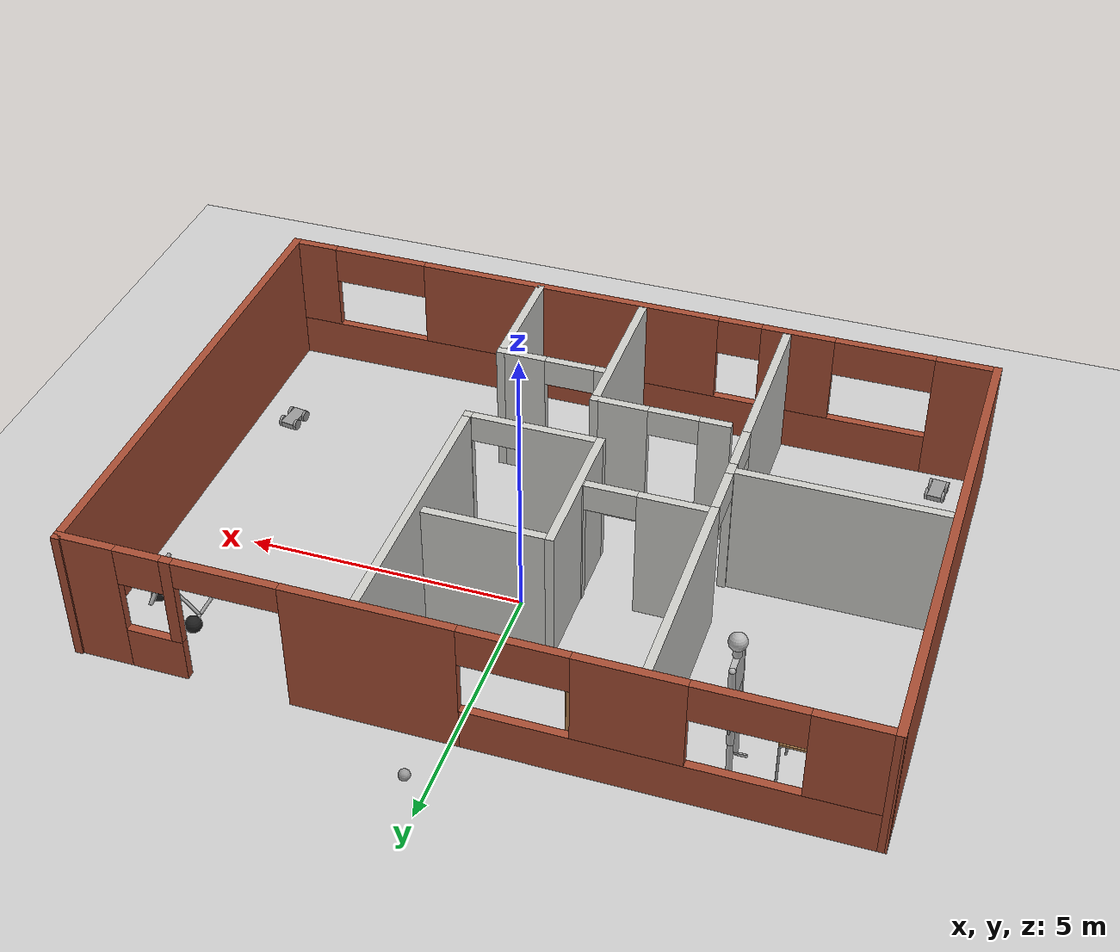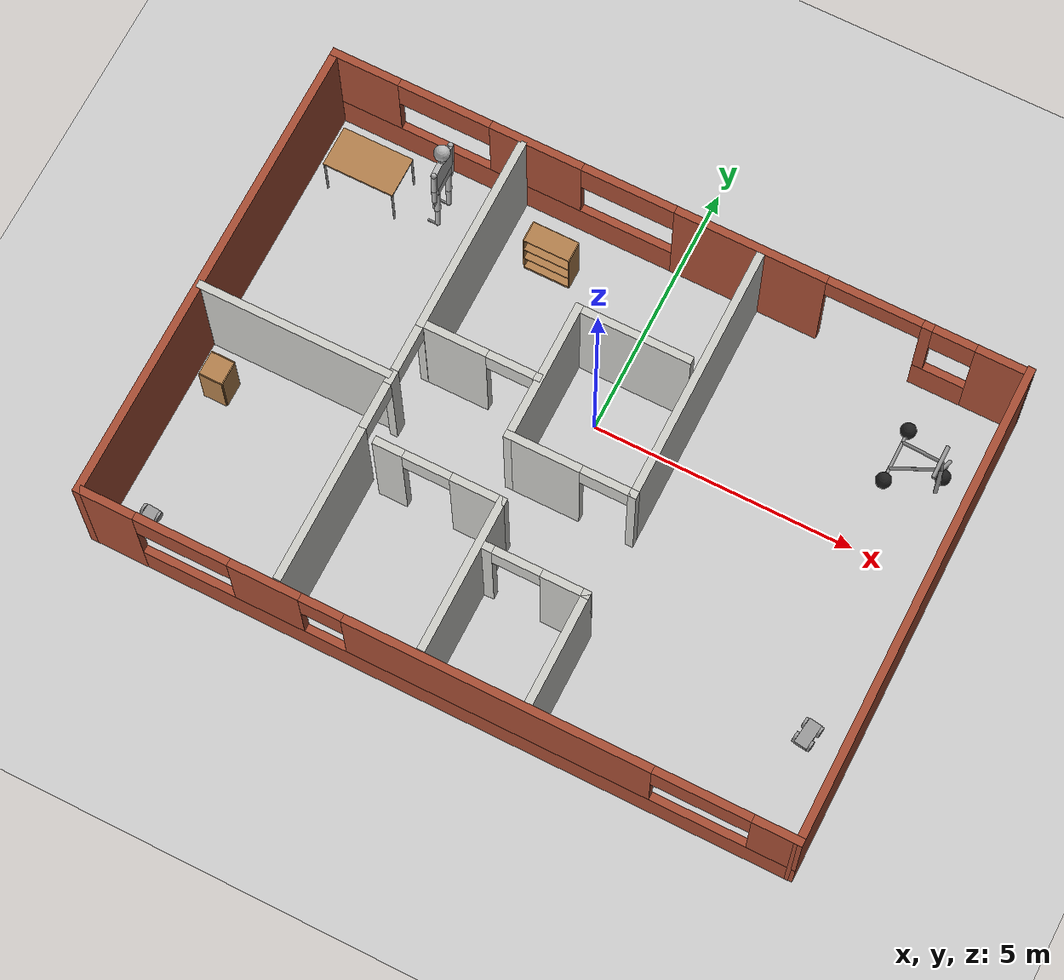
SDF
<sdf version="1.6">
 <world name="default">
  <plugin name="welcome" filename="libwelcome.so"/>
  <light name="sun" type="directional">
   <pose>0 0 10 0 -0 0</pose>
   <diffuse>0.8 0.8 0.8 1</diffuse>
   <specular>0.1 0.1 0.1 1</specular>
   <attenuation>
    <range>1000</range>
    <constant>0.9</constant>
    <linear>0.01</linear>
    <quadratic>0.001</quadratic>
   </attenuation>
   <direction>-0.5 0.5 -1</direction>
  </light>
  <model name="ground_plane">
   <static>1</static>
   <link name="link">
    <collision name="collision">
     <geometry><plane><normal>0 0 1</normal><size>100 100</size></plane></geometry>
     <surface><friction><ode><mu>100</mu><mu2>50</mu2></ode></friction></surface>
    </collision>
    <visual name="visual">
     <cast_shadows>0</cast_shadows>
     <geometry><plane><normal>0 0 1</normal><size>100 100</size></plane></geometry>
     <material>
      <script><uri>file://media/materials/scripts/gazebo.material</uri><name>Gazebo/Grey</name></script>
     </material>
    </visual>
   </link>
  </model>
  <gravity>0 0 -9.8</gravity>
  <magnetic_field>6e-06 2.3e-05 -4.2e-05</magnetic_field>
  <atmosphere type="adiabatic"/>
  <physics name="default_physics" default="0" type="ode">
   <max_step_size>0.001</max_step_size>
   <real_time_factor>1</real_time_factor>
   <real_time_update_rate>1000</real_time_update_rate>
  </physics>
  <scene><ambient>0.4 0.4 0.4 1</ambient><background>0.7 0.7 0.7 1</background><shadows>1</shadows></scene>
  <spherical_coordinates>
   <surface_model>EARTH_WGS84</surface_model>
   <latitude_deg>0</latitude_deg>
   <longitude_deg>0</longitude_deg>
   <elevation>0</elevation>
   <heading_deg>0</heading_deg>
  </spherical_coordinates>
  <model name="myhouse">
   <pose>-0.15107 -1.18203 0 0 -0 0</pose>
   <link name="Wall_38">
    <collision name="Wall_38_Collision">
     <geometry><box><size>9.28418 0.15 2.5</size></box></geometry>
     <pose>0 0 1.25 0 -0 0</pose>
    </collision>
    <visual name="Wall_38_Visual">
     <pose>0 0 1.25 0 -0 0</pose>
     <geometry><box><size>9.28418 0.15 2.5</size></box></geometry>
     <material>
      <script><uri>file://media/materials/scripts/gazebo.material</uri><name>Gazebo/Bricks</name></script>
      <ambient>0.996078 0.47451 0.0196078 1</ambient>
     </material>
    </visual>
    <pose>-6.69036 -4.9e-05 0 0 0 -1.5708</pose>
   </link>
   <link name="Wall_39">
    <pose>0.000136 -4.56705 0 0 -0 0</pose>
    <visual name="Wall_39_Visual_0">
     <pose>-6.18995 0 1.25 0 -0 0</pose>
     <geometry><box><size>1.1511 0.15 2.5</size></box></geometry>
     <material>
      <script><uri>file://media/materials/scripts/gazebo.material</uri><name>Gazebo/Bricks</name></script>
      <ambient>0.996078 0.47451 0.0196078 1</ambient>
     </material>
    </visual>
    <collision name="Wall_39_Collision_0">
     <geometry><box><size>1.1511 0.15 2.5</size></box></geometry>
     <pose>-6.18995 0 1.25 0 -0 0</pose>
    </collision>
    <visual name="Wall_39_Visual_1">
     <pose>0.575549 0 0.4 0 -0 0</pose>
     <geometry><box><size>12.3799 0.15 0.8</size></box></geometry>
     <material>
      <script><uri>file://media/materials/scripts/gazebo.material</uri><name>Gazebo/Bricks</name></script>
      <ambient>0.996078 0.47451 0.0196078 1</ambient>
     </material>
    </visual>
    <collision name="Wall_39_Collision_1">
     <geometry><box><size>12.3799 0.15 0.8</size></box></geometry>
     <pose>0.575549 0 0.4 0 -0 0</pose>
    </collision>
    <visual name="Wall_39_Visual_2">
     <pose>-3.14182 0 1.65 0 -0 0</pose>
     <geometry><box><size>1.34517 0.15 1.7</size></box></geometry>
     <material>
      <script><uri>file://media/materials/scripts/gazebo.material</uri><name>Gazebo/Bricks</name></script>
      <ambient>0.996078 0.47451 0.0196078 1</ambient>
     </material>
    </visual>
    <collision name="Wall_39_Collision_2">
     <geometry><box><size>1.34517 0.15 1.7</size></box></geometry>
     <pose>-3.14182 0 1.65 0 -0 0</pose>
    </collision>
    <visual name="Wall_39_Visual_3">
     <pose>1.19211 0 1.65 0 -0 0</pose>
     <geometry><box><size>5.72269 0.15 1.7</size></box></geometry>
     <material>
      <script><uri>file://media/materials/scripts/gazebo.material</uri><name>Gazebo/Bricks</name></script>
      <ambient>0.996078 0.47451 0.0196078 1</ambient>
     </material>
    </visual>
    <collision name="Wall_39_Collision_3">
     <geometry><box><size>5.72269 0.15 1.7</size></box></geometry>
     <pose>1.19211 0 1.65 0 -0 0</pose>
    </collision>
    <visual name="Wall_39_Visual_4">
     <pose>6.30948 0 1.65 0 -0 0</pose>
     <geometry><box><size>0.912041 0.15 1.7</size></box></geometry>
     <material>
      <script><uri>file://media/materials/scripts/gazebo.material</uri><name>Gazebo/Bricks</name></script>
      <ambient>0.996078 0.47451 0.0196078 1</ambient>
     </material>
    </visual>
    <collision name="Wall_39_Collision_4">
     <geometry><box><size>0.912041 0.15 1.7</size></box></geometry>
     <pose>6.30948 0 1.65 0 -0 0</pose>
    </collision>
    <visual name="Wall_39_Visual_5">
     <pose>-4.7144 0 2.15 0 -0 0</pose>
     <geometry><box><size>1.8 0.15 0.7</size></box></geometry>
     <material>
      <script><uri>file://media/materials/scripts/gazebo.material</uri><name>Gazebo/Bricks</name></script>
      <ambient>0.996078 0.47451 0.0196078 1</ambient>
     </material>
    </visual>
    <collision name="Wall_39_Collision_5">
     <geometry><box><size>1.8 0.15 0.7</size></box></geometry>
     <pose>-4.7144 0 2.15 0 -0 0</pose>
    </collision>
    <visual name="Wall_39_Visual_6">
     <pose>-2.06923 0 2.15 0 -0 0</pose>
     <geometry><box><size>0.8 0.15 0.7</size></box></geometry>
     <material>
      <script><uri>file://media/materials/scripts/gazebo.material</uri><name>Gazebo/Bricks</name></script>
      <ambient>0.996078 0.47451 0.0196078 1</ambient>
     </material>
    </visual>
    <collision name="Wall_39_Collision_6">
     <geometry><box><size>0.8 0.15 0.7</size></box></geometry>
     <pose>-2.06923 0 2.15 0 -0 0</pose>
    </collision>
    <visual name="Wall_39_Visual_7">
     <pose>4.95346 0 2.15 0 -0 0</pose>
     <geometry><box><size>1.8 0.15 0.7</size></box></geometry>
     <material>
      <script><uri>file://media/materials/scripts/gazebo.material</uri><name>Gazebo/Bricks</name></script>
      <ambient>0.996078 0.47451 0.0196078 1</ambient>
     </material>
    </visual>
    <collision name="Wall_39_Collision_7">
     <geometry><box><size>1.8 0.15 0.7</size></box></geometry>
     <pose>4.95346 0 2.15 0 -0 0</pose>
    </collision>
   </link>
   <link name="Wall_40">
    <collision name="Wall_40_Collision">
     <geometry><box><size>9.28418 0.15 2.5</size></box></geometry>
     <pose>0 0 1.25 0 -0 0</pose>
    </collision>
    <visual name="Wall_40_Visual">
     <pose>0 0 1.25 0 -0 0</pose>
     <geometry><box><size>9.28418 0.15 2.5</size></box></geometry>
     <material>
      <script><uri>file://media/materials/scripts/gazebo.material</uri><name>Gazebo/Bricks</name></script>
      <ambient>0.996078 0.47451 0.0196078 1</ambient>
     </material>
    </visual>
    <pose>6.69014 4.1e-05 0 0 -0 1.57091</pose>
   </link>
   <link name="Wall_41">
    <pose>-0.000364 4.55175 0 0 -0 3.13932</pose>
    <visual name="Wall_41_Visual_0">
     <pose>-6.23299 0 1.25 0 -0 0</pose>
     <geometry><box><size>1.06429 0.15 2.5</size></box></geometry>
     <material>
      <script><uri>file://media/materials/scripts/gazebo.material</uri><name>Gazebo/Bricks</name></script>
      <ambient>0.996078 0.47451 0.0196078 1</ambient>
     </material>
    </visual>
    <collision name="Wall_41_Collision_0">
     <geometry><box><size>1.06429 0.15 2.5</size></box></geometry>
     <pose>-6.23299 0 1.25 0 -0 0</pose>
    </collision>
    <visual name="Wall_41_Visual_1">
     <pose>-1.44735 0 1.25 0 -0 0</pose>
     <geometry><box><size>2.90668 0.15 2.5</size></box></geometry>
     <material>
      <script><uri>file://media/materials/scripts/gazebo.material</uri><name>Gazebo/Bricks</name></script>
      <ambient>0.996078 0.47451 0.0196078 1</ambient>
     </material>
    </visual>
    <collision name="Wall_41_Collision_1">
     <geometry><box><size>2.90668 0.15 2.5</size></box></geometry>
     <pose>-1.44735 0 1.25 0 -0 0</pose>
    </collision>
    <visual name="Wall_41_Visual_2">
     <pose>-5.20076 0 0.4 0 -0 0</pose>
     <geometry><box><size>1.00016 0.15 0.8</size></box></geometry>
     <material>
      <script><uri>file://media/materials/scripts/gazebo.material</uri><name>Gazebo/Bricks</name></script>
      <ambient>0.996078 0.47451 0.0196078 1</ambient>
     </material>
    </visual>
    <collision name="Wall_41_Collision_2">
     <geometry><box><size>1.00016 0.15 0.8</size></box></geometry>
     <pose>-5.20076 0 0.4 0 -0 0</pose>
    </collision>
    <visual name="Wall_41_Visual_3">
     <pose>3.38556 0 0.4 0 -0 0</pose>
     <geometry><box><size>6.75914 0.15 0.8</size></box></geometry>
     <material>
      <script><uri>file://media/materials/scripts/gazebo.material</uri><name>Gazebo/Bricks</name></script>
      <ambient>0.996078 0.47451 0.0196078 1</ambient>
     </material>
    </visual>
    <collision name="Wall_41_Collision_3">
     <geometry><box><size>6.75914 0.15 0.8</size></box></geometry>
     <pose>3.38556 0 0.4 0 -0 0</pose>
    </collision>
    <visual name="Wall_41_Visual_4">
     <pose>-4.80076 0 1.65 0 -0 0</pose>
     <geometry><box><size>0.200157 0.15 1.7</size></box></geometry>
     <material>
      <script><uri>file://media/materials/scripts/gazebo.material</uri><name>Gazebo/Bricks</name></script>
      <ambient>0.996078 0.47451 0.0196078 1</ambient>
     </material>
    </visual>
    <collision name="Wall_41_Collision_4">
     <geometry><box><size>0.200157 0.15 1.7</size></box></geometry>
     <pose>-4.80076 0 1.65 0 -0 0</pose>
    </collision>
    <visual name="Wall_41_Visual_5">
     <pose>-4.80076 0 1.65 0 -0 0</pose>
     <geometry><box><size>0.200157 0.15 1.7</size></box></geometry>
     <material>
      <script><uri>file://media/materials/scripts/gazebo.material</uri><name>Gazebo/Bricks</name></script>
      <ambient>0.996078 0.47451 0.0196078 1</ambient>
     </material>
    </visual>
    <collision name="Wall_41_Collision_5">
     <geometry><box><size>0.200157 0.15 1.7</size></box></geometry>
     <pose>-4.80076 0 1.65 0 -0 0</pose>
    </collision>
    <visual name="Wall_41_Visual_6">
     <pose>2.70554 0 1.65 0 -0 0</pose>
     <geometry><box><size>1.79911 0.15 1.7</size></box></geometry>
     <material>
      <script><uri>file://media/materials/scripts/gazebo.material</uri><name>Gazebo/Bricks</name></script>
      <ambient>0.996078 0.47451 0.0196078 1</ambient>
     </material>
    </visual>
    <collision name="Wall_41_Collision_6">
     <geometry><box><size>1.79911 0.15 1.7</size></box></geometry>
     <pose>2.70554 0 1.65 0 -0 0</pose>
    </collision>
    <visual name="Wall_41_Visual_7">
     <pose>6.08511 0 1.65 0 -0 0</pose>
     <geometry><box><size>1.36003 0.15 1.7</size></box></geometry>
     <material>
      <script><uri>file://media/materials/scripts/gazebo.material</uri><name>Gazebo/Bricks</name></script>
      <ambient>0.996078 0.47451 0.0196078 1</ambient>
     </material>
    </visual>
    <collision name="Wall_41_Collision_7">
     <geometry><box><size>1.36003 0.15 1.7</size></box></geometry>
     <pose>6.08511 0 1.65 0 -0 0</pose>
    </collision>
    <visual name="Wall_41_Visual_8">
     <pose>-5.30084 0 2.15 0 -0 0</pose>
     <geometry><box><size>0.8 0.15 0.7</size></box></geometry>
     <material>
      <script><uri>file://media/materials/scripts/gazebo.material</uri><name>Gazebo/Bricks</name></script>
      <ambient>0.996078 0.47451 0.0196078 1</ambient>
     </material>
    </visual>
    <collision name="Wall_41_Collision_8">
     <geometry><box><size>0.8 0.15 0.7</size></box></geometry>
     <pose>-5.30084 0 2.15 0 -0 0</pose>
    </collision>
    <visual name="Wall_41_Visual_9">
     <pose>0.905991 0 2.15 0 -0 0</pose>
     <geometry><box><size>1.8 0.15 0.7</size></box></geometry>
     <material>
      <script><uri>file://media/materials/scripts/gazebo.material</uri><name>Gazebo/Bricks</name></script>
      <ambient>0.996078 0.47451 0.0196078 1</ambient>
     </material>
    </visual>
    <collision name="Wall_41_Collision_9">
     <geometry><box><size>1.8 0.15 0.7</size></box></geometry>
     <pose>0.905991 0 2.15 0 -0 0</pose>
    </collision>
    <visual name="Wall_41_Visual_10">
     <pose>4.5051 0 2.15 0 -0 0</pose>
     <geometry><box><size>1.8 0.15 0.7</size></box></geometry>
     <material>
      <script><uri>file://media/materials/scripts/gazebo.material</uri><name>Gazebo/Bricks</name></script>
      <ambient>0.996078 0.47451 0.0196078 1</ambient>
     </material>
    </visual>
    <collision name="Wall_41_Collision_10">
     <geometry><box><size>1.8 0.15 0.7</size></box></geometry>
     <pose>4.5051 0 2.15 0 -0 0</pose>
    </collision>
    <visual name="Wall_41_Visual_11">
     <pose>-3.80068 0 2.25 0 -0 0</pose>
     <geometry><box><size>1.8 0.15 0.5</size></box></geometry>
     <material>
      <script><uri>file://media/materials/scripts/gazebo.material</uri><name>Gazebo/Bricks</name></script>
      <ambient>0.996078 0.47451 0.0196078 1</ambient>
     </material>
    </visual>
    <collision name="Wall_41_Collision_11">
     <geometry><box><size>1.8 0.15 0.5</size></box></geometry>
     <pose>-3.80068 0 2.25 0 -0 0</pose>
    </collision>
    <visual name="Wall_41_Visual_12">
     <pose>-3.80068 0 2.25 0 -0 0</pose>
     <geometry><box><size>1.8 0.15 0.5</size></box></geometry>
     <material>
      <script><uri>file://media/materials/scripts/gazebo.material</uri><name>Gazebo/Bricks</name></script>
      <ambient>0.996078 0.47451 0.0196078 1</ambient>
     </material>
    </visual>
    <collision name="Wall_41_Collision_12">
     <geometry><box><size>1.8 0.15 0.5</size></box></geometry>
     <pose>-3.80068 0 2.25 0 -0 0</pose>
    </collision>
   </link>
   <link name="Wall_43">
    <pose>-2.95236 0.022951 0 0 0 -1.5708</pose>
    <visual name="Wall_43_Visual_0">
     <pose>-2.54618 0 1.25 0 -0 0</pose>
     <geometry><box><size>3.90763 0.15 2.5</size></box></geometry>
     <material>
      <script><uri>file://media/materials/scripts/gazebo.material</uri><name>Gazebo/CeilingTiled</name></script>
      <ambient>0.760784 0.662745 0.627451 1</ambient>
     </material>
    </visual>
    <collision name="Wall_43_Collision_0">
     <geometry><box><size>3.90763 0.15 2.5</size></box></geometry>
     <pose>-2.54618 0 1.25 0 -0 0</pose>
    </collision>
    <visual name="Wall_43_Visual_1">
     <pose>0.442836 0 1.25 0 -0 0</pose>
     <geometry><box><size>0.270409 0.15 2.5</size></box></geometry>
     <material>
      <script><uri>file://media/materials/scripts/gazebo.material</uri><name>Gazebo/CeilingTiled</name></script>
      <ambient>0.760784 0.662745 0.627451 1</ambient>
     </material>
    </visual>
    <collision name="Wall_43_Collision_1">
     <geometry><box><size>0.270409 0.15 2.5</size></box></geometry>
     <pose>0.442836 0 1.25 0 -0 0</pose>
    </collision>
    <visual name="Wall_43_Visual_2">
     <pose>2.98902 0 1.25 0 -0 0</pose>
     <geometry><box><size>3.02196 0.15 2.5</size></box></geometry>
     <material>
      <script><uri>file://media/materials/scripts/gazebo.material</uri><name>Gazebo/CeilingTiled</name></script>
      <ambient>0.760784 0.662745 0.627451 1</ambient>
     </material>
    </visual>
    <collision name="Wall_43_Collision_2">
     <geometry><box><size>3.02196 0.15 2.5</size></box></geometry>
     <pose>2.98902 0 1.25 0 -0 0</pose>
    </collision>
    <visual name="Wall_43_Visual_3">
     <pose>-0.142368 0 2.25 0 -0 0</pose>
     <geometry><box><size>0.9 0.15 0.5</size></box></geometry>
     <material>
      <script><uri>file://media/materials/scripts/gazebo.material</uri><name>Gazebo/CeilingTiled</name></script>
      <ambient>0.760784 0.662745 0.627451 1</ambient>
     </material>
    </visual>
    <collision name="Wall_43_Collision_3">
     <geometry><box><size>0.9 0.15 0.5</size></box></geometry>
     <pose>-0.142368 0 2.25 0 -0 0</pose>
    </collision>
    <visual name="Wall_43_Visual_4">
     <pose>1.02804 0 2.25 0 -0 0</pose>
     <geometry><box><size>0.9 0.15 0.5</size></box></geometry>
     <material>
      <script><uri>file://media/materials/scripts/gazebo.material</uri><name>Gazebo/CeilingTiled</name></script>
      <ambient>0.760784 0.662745 0.627451 1</ambient>
     </material>
    </visual>
    <collision name="Wall_43_Collision_4">
     <geometry><box><size>0.9 0.15 0.5</size></box></geometry>
     <pose>1.02804 0 2.25 0 -0 0</pose>
    </collision>
   </link>
   <link name="Wall_45">
    <collision name="Wall_45_Collision">
     <geometry><box><size>3.75 0.15 2.5</size></box></geometry>
     <pose>0 0 1.25 0 -0 0</pose>
    </collision>
    <visual name="Wall_45_Visual">
     <pose>0 0 1.25 0 -0 0</pose>
     <geometry><box><size>3.75 0.15 2.5</size></box></geometry>
     <material>
      <script><uri>file://media/materials/scripts/gazebo.material</uri><name>Gazebo/CeilingTiled</name></script>
      <ambient>0.760784 0.662745 0.627451 1</ambient>
     </material>
    </visual>
    <pose>-4.83736 -0.389049 0 0 -0 0</pose>
   </link>
   <link name="Wall_47">
    <pose>-1.77981 0.698376 0 0 -0 0</pose>
    <visual name="Wall_47_Visual_0">
     <pose>-0.514494 0 1.25 0 -0 0</pose>
     <geometry><box><size>1.22101 0.15 2.5</size></box></geometry>
     <material>
      <script><uri>file://media/materials/scripts/gazebo.material</uri><name>Gazebo/CeilingTiled</name></script>
      <ambient>0.760784 0.662745 0.627451 1</ambient>
     </material>
    </visual>
    <collision name="Wall_47_Collision_0">
     <geometry><box><size>1.22101 0.15 2.5</size></box></geometry>
     <pose>-0.514494 0 1.25 0 -0 0</pose>
    </collision>
    <visual name="Wall_47_Visual_1">
     <pose>1.06051 0 1.25 0 -0 0</pose>
     <geometry><box><size>0.128988 0.15 2.5</size></box></geometry>
     <material>
      <script><uri>file://media/materials/scripts/gazebo.material</uri><name>Gazebo/CeilingTiled</name></script>
      <ambient>0.760784 0.662745 0.627451 1</ambient>
     </material>
    </visual>
    <collision name="Wall_47_Collision_1">
     <geometry><box><size>0.128988 0.15 2.5</size></box></geometry>
     <pose>1.06051 0 1.25 0 -0 0</pose>
    </collision>
    <visual name="Wall_47_Visual_2">
     <pose>0.546012 0 2.25 0 -0 0</pose>
     <geometry><box><size>0.9 0.15 0.5</size></box></geometry>
     <material>
      <script><uri>file://media/materials/scripts/gazebo.material</uri><name>Gazebo/CeilingTiled</name></script>
      <ambient>0.760784 0.662745 0.627451 1</ambient>
     </material>
    </visual>
    <collision name="Wall_47_Collision_2">
     <geometry><box><size>0.9 0.15 0.5</size></box></geometry>
     <pose>0.546012 0 2.25 0 -0 0</pose>
    </collision>
   </link>
   <link name="Wall_49">
    <collision name="Wall_49_Collision">
     <geometry><box><size>5 0.15 2.5</size></box></geometry>
     <pose>0 0 1.25 0 -0 0</pose>
    </collision>
    <visual name="Wall_49_Visual">
     <pose>0 0 1.25 0 -0 0</pose>
     <geometry><box><size>5 0.15 2.5</size></box></geometry>
     <material>
      <script><uri>file://media/materials/scripts/gazebo.material</uri><name>Gazebo/CeilingTiled</name></script>
      <ambient>0.760784 0.662745 0.627451 1</ambient>
     </material>
    </visual>
    <pose>1.66164 1.97395 0 0 0 -1.5708</pose>
   </link>
   <link name="Wall_50">
    <pose>0.486636 -0.451049 0 0 -0 3.14159</pose>
    <visual name="Wall_50_Visual_0">
     <pose>-1.17305 0 1.25 0 -0 0</pose>
     <geometry><box><size>0.153899 0.15 2.5</size></box></geometry>
     <material>
      <script><uri>file://media/materials/scripts/gazebo.material</uri><name>Gazebo/CeilingTiled</name></script>
      <ambient>0.760784 0.662745 0.627451 1</ambient>
     </material>
    </visual>
    <collision name="Wall_50_Collision_0">
     <geometry><box><size>0.153899 0.15 2.5</size></box></geometry>
     <pose>-1.17305 0 1.25 0 -0 0</pose>
    </collision>
    <visual name="Wall_50_Visual_1">
     <pose>0.526949 0 1.25 0 -0 0</pose>
     <geometry><box><size>1.4461 0.15 2.5</size></box></geometry>
     <material>
      <script><uri>file://media/materials/scripts/gazebo.material</uri><name>Gazebo/CeilingTiled</name></script>
      <ambient>0.760784 0.662745 0.627451 1</ambient>
     </material>
    </visual>
    <collision name="Wall_50_Collision_1">
     <geometry><box><size>1.4461 0.15 2.5</size></box></geometry>
     <pose>0.526949 0 1.25 0 -0 0</pose>
    </collision>
    <visual name="Wall_50_Visual_2">
     <pose>-0.646101 0 2.25 0 -0 0</pose>
     <geometry><box><size>0.9 0.15 0.5</size></box></geometry>
     <material>
      <script><uri>file://media/materials/scripts/gazebo.material</uri><name>Gazebo/CeilingTiled</name></script>
      <ambient>0.760784 0.662745 0.627451 1</ambient>
     </material>
    </visual>
    <collision name="Wall_50_Collision_2">
     <geometry><box><size>0.9 0.15 0.5</size></box></geometry>
     <pose>-0.646101 0 2.25 0 -0 0</pose>
    </collision>
   </link>
   <link name="Wall_51">
    <collision name="Wall_51_Collision">
     <geometry><box><size>2.75 0.15 2.5</size></box></geometry>
     <pose>0 0 1.25 0 -0 0</pose>
    </collision>
    <visual name="Wall_51_Visual">
     <pose>0 0 1.25 0 -0 0</pose>
     <geometry><box><size>2.75 0.15 2.5</size></box></geometry>
     <material>
      <script><uri>file://media/materials/scripts/gazebo.material</uri><name>Gazebo/CeilingTiled</name></script>
      <ambient>0.760784 0.662745 0.627451 1</ambient>
     </material>
    </visual>
    <pose>-0.688364 0.848951 0 0 -0 1.5708</pose>
   </link>
   <link name="Wall_52">
    <collision name="Wall_52_Collision">
     <geometry><box><size>2.25 0.15 2.5</size></box></geometry>
     <pose>0 0 1.25 0 -0 0</pose>
    </collision>
    <visual name="Wall_52_Visual">
     <pose>0 0 1.25 0 -0 0</pose>
     <geometry><box><size>2.25 0.15 2.5</size></box></geometry>
     <material>
      <script><uri>file://media/materials/scripts/gazebo.material</uri><name>Gazebo/CeilingTiled</name></script>
      <ambient>0.760784 0.662745 0.627451 1</ambient>
     </material>
    </visual>
    <pose>0.361636 2.14895 0 0 -0 0</pose>
   </link>
   <link name="Wall_54">
    <collision name="Wall_54_Collision">
     <geometry><box><size>2.25 0.15 2.5</size></box></geometry>
     <pose>0 0 1.25 0 -0 0</pose>
    </collision>
    <visual name="Wall_54_Visual">
     <pose>0 0 1.25 0 -0 0</pose>
     <geometry><box><size>2.25 0.15 2.5</size></box></geometry>
     <material>
      <script><uri>file://media/materials/scripts/gazebo.material</uri><name>Gazebo/CeilingTiled</name></script>
      <ambient>0.760784 0.662745 0.627451 1</ambient>
     </material>
    </visual>
    <pose>1.74164 -3.43505 0 0 -0 1.5708</pose>
   </link>
   <link name="Wall_55">
    <pose>0.816636 -2.38505 0 0 -0 3.14159</pose>
    <visual name="Wall_55_Visual_0">
     <pose>-0.547756 0 1.25 0 -0 0</pose>
     <geometry><box><size>0.904487 0.15 2.5</size></box></geometry>
     <material>
      <script><uri>file://media/materials/scripts/gazebo.material</uri><name>Gazebo/CeilingTiled</name></script>
      <ambient>0.760784 0.662745 0.627451 1</ambient>
     </material>
    </visual>
    <collision name="Wall_55_Collision_0">
     <geometry><box><size>0.904487 0.15 2.5</size></box></geometry>
     <pose>-0.547756 0 1.25 0 -0 0</pose>
    </collision>
    <visual name="Wall_55_Visual_1">
     <pose>0.902244 0 1.25 0 -0 0</pose>
     <geometry><box><size>0.195513 0.15 2.5</size></box></geometry>
     <material>
      <script><uri>file://media/materials/scripts/gazebo.material</uri><name>Gazebo/CeilingTiled</name></script>
      <ambient>0.760784 0.662745 0.627451 1</ambient>
     </material>
    </visual>
    <collision name="Wall_55_Collision_1">
     <geometry><box><size>0.195513 0.15 2.5</size></box></geometry>
     <pose>0.902244 0 1.25 0 -0 0</pose>
    </collision>
    <visual name="Wall_55_Visual_2">
     <pose>0.354487 0 2.25 0 -0 0</pose>
     <geometry><box><size>0.9 0.15 0.5</size></box></geometry>
     <material>
      <script><uri>file://media/materials/scripts/gazebo.material</uri><name>Gazebo/CeilingTiled</name></script>
      <ambient>0.760784 0.662745 0.627451 1</ambient>
     </material>
    </visual>
    <collision name="Wall_55_Collision_2">
     <geometry><box><size>0.9 0.15 0.5</size></box></geometry>
     <pose>0.354487 0 2.25 0 -0 0</pose>
    </collision>
   </link>
   <link name="Wall_57">
    <collision name="Wall_57_Collision">
     <geometry><box><size>3 0.15 2.5</size></box></geometry>
     <pose>0 0 1.25 0 -0 0</pose>
    </collision>
    <visual name="Wall_57_Visual">
     <pose>0 0 1.25 0 -0 0</pose>
     <geometry><box><size>3 0.15 2.5</size></box></geometry>
     <material>
      <script><uri>file://media/materials/scripts/gazebo.material</uri><name>Gazebo/CeilingTiled</name></script>
      <ambient>0.760784 0.662745 0.627451 1</ambient>
     </material>
    </visual>
    <pose>-0.253364 -2.98005 0 0 -0 1.5708</pose>
   </link>
   <link name="Wall_58">
    <pose>-1.42836 -1.55505 0 0 -0 3.14159</pose>
    <visual name="Wall_58_Visual_0">
     <pose>-0.732595 0 1.25 0 -0 0</pose>
     <geometry><box><size>1.03481 0.15 2.5</size></box></geometry>
     <material>
      <script><uri>file://media/materials/scripts/gazebo.material</uri><name>Gazebo/CeilingTiled</name></script>
      <ambient>0.760784 0.662745 0.627451 1</ambient>
     </material>
    </visual>
    <collision name="Wall_58_Collision_0">
     <geometry><box><size>1.03481 0.15 2.5</size></box></geometry>
     <pose>-0.732595 0 1.25 0 -0 0</pose>
    </collision>
    <visual name="Wall_58_Visual_1">
     <pose>0.967405 0 1.25 0 -0 0</pose>
     <geometry><box><size>0.565189 0.15 2.5</size></box></geometry>
     <material>
      <script><uri>file://media/materials/scripts/gazebo.material</uri><name>Gazebo/CeilingTiled</name></script>
      <ambient>0.760784 0.662745 0.627451 1</ambient>
     </material>
    </visual>
    <collision name="Wall_58_Collision_1">
     <geometry><box><size>0.565189 0.15 2.5</size></box></geometry>
     <pose>0.967405 0 1.25 0 -0 0</pose>
    </collision>
    <visual name="Wall_58_Visual_2">
     <pose>0.234811 0 2.25 0 -0 0</pose>
     <geometry><box><size>0.9 0.15 0.5</size></box></geometry>
     <material>
      <script><uri>file://media/materials/scripts/gazebo.material</uri><name>Gazebo/CeilingTiled</name></script>
      <ambient>0.760784 0.662745 0.627451 1</ambient>
     </material>
    </visual>
    <collision name="Wall_58_Collision_2">
     <geometry><box><size>0.9 0.15 0.5</size></box></geometry>
     <pose>0.234811 0 2.25 0 -0 0</pose>
    </collision>
   </link>
   <static>1</static>
  </model>
  <model name="Car">
   <link name="link_0">
    <inertial>
     <mass>1</mass>
     <inertia>
      <ixx>0.166667</ixx>
      <ixy>0</ixy>
      <ixz>0</ixz>
      <iyy>0.166667</iyy>
      <iyz>0</iyz>
      <izz>0.166667</izz>
     </inertia>
    </inertial>
    <visual name="visual">
     <geometry><box><size>0.25 0.5 0.1</size></box></geometry>
     <material>
      <lighting>1</lighting>
      <script><uri>file://media/materials/scripts/gazebo.material</uri><name>Gazebo/Grey</name></script>
      <ambient>0.3 0.3 0.3 1</ambient>
      <diffuse>0.7 0.7 0.7 1</diffuse>
      <specular>0.01 0.01 0.01 1</specular>
      <emissive>0 0 0 1</emissive>
      <shader type="vertex"><normal_map>__default__</normal_map></shader>
     </material>
    </visual>
    <collision name="collision">
     <geometry><box><size>0.25 0.5 0.1</size></box></geometry>
     <surface>
      <friction>
       <ode><mu>1</mu><mu2>1</mu2><fdir1>0 0 0</fdir1><slip1>0</slip1><slip2>0</slip2></ode>
       <torsional>
        <coefficient>1</coefficient>
        <patch_radius>0</patch_radius>
        <surface_radius>0</surface_radius>
        <use_patch_radius>1</use_patch_radius>
        <ode><slip>0</slip></ode>
       </torsional>
      </friction>
      <bounce><restitution_coefficient>0</restitution_coefficient><threshold>1e+06</threshold></bounce>
      <contact>
       <collide_without_contact>0</collide_without_contact>
       <collide_without_contact_bitmask>1</collide_without_contact_bitmask>
       <collide_bitmask>1</collide_bitmask>
       <ode>
        <soft_cfm>0</soft_cfm>
        <soft_erp>0.2</soft_erp>
        <kp>1e+13</kp>
        <kd>1</kd>
        <max_vel>0.01</max_vel>
        <min_depth>0</min_depth>
       </ode>
       <bullet>
        <split_impulse>1</split_impulse>
        <split_impulse_penetration_threshold>-0.01</split_impulse_penetration_threshold>
        <soft_cfm>0</soft_cfm>
        <soft_erp>0.2</soft_erp>
        <kp>1e+13</kp>
        <kd>1</kd>
       </bullet>
      </contact>
     </surface>
    </collision>
   </link>
   <link name="link_1">
    <pose>-0.15001 0.15 0 0 1.5707 0</pose>
    <inertial>
     <mass>1</mass>
     <inertia><ixx>0.145833</ixx><ixy>0</ixy><ixz>0</ixz><iyy>0.145833</iyy><iyz>0</iyz><izz>0.125</izz></inertia>
    </inertial>
    <visual name="visual">
     <geometry><cylinder><radius>0.1</radius><length>0.05</length></cylinder></geometry>
     <material>
      <lighting>1</lighting>
      <script><uri>file://media/materials/scripts/gazebo.material</uri><name>Gazebo/Grey</name></script>
      <ambient>0.3 0.3 0.3 1</ambient>
      <diffuse>0.7 0.7 0.7 1</diffuse>
      <specular>0.01 0.01 0.01 1</specular>
      <emissive>0 0 0 1</emissive>
      <shader type="vertex"><normal_map>__default__</normal_map></shader>
     </material>
    </visual>
    <collision name="collision">
     <geometry><cylinder><radius>0.1</radius><length>0.05</length></cylinder></geometry>
     <surface>
      <friction>
       <ode><mu>1</mu><mu2>1</mu2><fdir1>0 0 0</fdir1><slip1>0</slip1><slip2>0</slip2></ode>
       <torsional>
        <coefficient>1</coefficient>
        <patch_radius>0</patch_radius>
        <surface_radius>0</surface_radius>
        <use_patch_radius>1</use_patch_radius>
        <ode><slip>0</slip></ode>
       </torsional>
      </friction>
      <bounce><restitution_coefficient>0</restitution_coefficient><threshold>1e+06</threshold></bounce>
      <contact>
       <collide_without_contact>0</collide_without_contact>
       <collide_without_contact_bitmask>1</collide_without_contact_bitmask>
       <collide_bitmask>1</collide_bitmask>
       <ode>
        <soft_cfm>0</soft_cfm>
        <soft_erp>0.2</soft_erp>
        <kp>1e+13</kp>
        <kd>1</kd>
        <max_vel>0.01</max_vel>
        <min_depth>0</min_depth>
       </ode>
       <bullet>
        <split_impulse>1</split_impulse>
        <split_impulse_penetration_threshold>-0.01</split_impulse_penetration_threshold>
        <soft_cfm>0</soft_cfm>
        <soft_erp>0.2</soft_erp>
        <kp>1e+13</kp>
        <kd>1</kd>
       </bullet>
      </contact>
     </surface>
    </collision>
   </link>
   <link name="link_1_clone">
    <pose>0.15001 -0.15 0 0 1.5707 0</pose>
    <inertial>
     <mass>1</mass>
     <inertia><ixx>0.145833</ixx><ixy>0</ixy><ixz>0</ixz><iyy>0.145833</iyy><iyz>0</iyz><izz>0.125</izz></inertia>
    </inertial>
    <visual name="visual">
     <geometry><cylinder><radius>0.1</radius><length>0.05</length></cylinder></geometry>
     <material>
      <lighting>1</lighting>
      <script><uri>file://media/materials/scripts/gazebo.material</uri><name>Gazebo/Grey</name></script>
      <ambient>0.3 0.3 0.3 1</ambient>
      <diffuse>0.7 0.7 0.7 1</diffuse>
      <specular>0.01 0.01 0.01 1</specular>
      <emissive>0 0 0 1</emissive>
      <shader type="vertex"><normal_map>__default__</normal_map></shader>
     </material>
    </visual>
    <collision name="collision">
     <geometry><cylinder><radius>0.1</radius><length>0.05</length></cylinder></geometry>
     <surface>
      <friction>
       <ode><mu>1</mu><mu2>1</mu2><fdir1>0 0 0</fdir1><slip1>0</slip1><slip2>0</slip2></ode>
       <torsional>
        <coefficient>1</coefficient>
        <patch_radius>0</patch_radius>
        <surface_radius>0</surface_radius>
        <use_patch_radius>1</use_patch_radius>
        <ode><slip>0</slip></ode>
       </torsional>
      </friction>
      <bounce><restitution_coefficient>0</restitution_coefficient><threshold>1e+06</threshold></bounce>
      <contact>
       <collide_without_contact>0</collide_without_contact>
       <collide_without_contact_bitmask>1</collide_without_contact_bitmask>
       <collide_bitmask>1</collide_bitmask>
       <ode>
        <soft_cfm>0</soft_cfm>
        <soft_erp>0.2</soft_erp>
        <kp>1e+13</kp>
        <kd>1</kd>
        <max_vel>0.01</max_vel>
        <min_depth>0</min_depth>
       </ode>
       <bullet>
        <split_impulse>1</split_impulse>
        <split_impulse_penetration_threshold>-0.01</split_impulse_penetration_threshold>
        <soft_cfm>0</soft_cfm>
        <soft_erp>0.2</soft_erp>
        <kp>1e+13</kp>
        <kd>1</kd>
       </bullet>
      </contact>
     </surface>
    </collision>
   </link>
   <link name="link_1_clone_0">
    <pose>-0.15001 -0.15 0 0 1.5707 0</pose>
    <inertial>
     <mass>1</mass>
     <inertia><ixx>0.145833</ixx><ixy>0</ixy><ixz>0</ixz><iyy>0.145833</iyy><iyz>0</iyz><izz>0.125</izz></inertia>
    </inertial>
    <visual name="visual">
     <geometry><cylinder><radius>0.1</radius><length>0.05</length></cylinder></geometry>
     <material>
      <lighting>1</lighting>
      <script><uri>file://media/materials/scripts/gazebo.material</uri><name>Gazebo/Grey</name></script>
      <ambient>0.3 0.3 0.3 1</ambient>
      <diffuse>0.7 0.7 0.7 1</diffuse>
      <specular>0.01 0.01 0.01 1</specular>
      <emissive>0 0 0 1</emissive>
      <shader type="vertex"><normal_map>__default__</normal_map></shader>
     </material>
    </visual>
    <collision name="collision">
     <geometry><cylinder><radius>0.1</radius><length>0.05</length></cylinder></geometry>
     <surface>
      <friction>
       <ode><mu>1</mu><mu2>1</mu2><fdir1>0 0 0</fdir1><slip1>0</slip1><slip2>0</slip2></ode>
       <torsional>
        <coefficient>1</coefficient>
        <patch_radius>0</patch_radius>
        <surface_radius>0</surface_radius>
        <use_patch_radius>1</use_patch_radius>
        <ode><slip>0</slip></ode>
       </torsional>
      </friction>
      <bounce><restitution_coefficient>0</restitution_coefficient><threshold>1e+06</threshold></bounce>
      <contact>
       <collide_without_contact>0</collide_without_contact>
       <collide_without_contact_bitmask>1</collide_without_contact_bitmask>
       <collide_bitmask>1</collide_bitmask>
       <ode>
        <soft_cfm>0</soft_cfm>
        <soft_erp>0.2</soft_erp>
        <kp>1e+13</kp>
        <kd>1</kd>
        <max_vel>0.01</max_vel>
        <min_depth>0</min_depth>
       </ode>
       <bullet>
        <split_impulse>1</split_impulse>
        <split_impulse_penetration_threshold>-0.01</split_impulse_penetration_threshold>
        <soft_cfm>0</soft_cfm>
        <soft_erp>0.2</soft_erp>
        <kp>1e+13</kp>
        <kd>1</kd>
       </bullet>
      </contact>
     </surface>
    </collision>
   </link>
   <link name="link_1_clone_clone">
    <pose>0.15001 0.15 0 0 1.5707 0</pose>
    <inertial>
     <mass>1</mass>
     <inertia><ixx>0.145833</ixx><ixy>0</ixy><ixz>0</ixz><iyy>0.145833</iyy><iyz>0</iyz><izz>0.125</izz></inertia>
    </inertial>
    <visual name="visual">
     <geometry><cylinder><radius>0.1</radius><length>0.05</length></cylinder></geometry>
     <material>
      <lighting>1</lighting>
      <script><uri>file://media/materials/scripts/gazebo.material</uri><name>Gazebo/Grey</name></script>
      <ambient>0.3 0.3 0.3 1</ambient>
      <diffuse>0.7 0.7 0.7 1</diffuse>
      <specular>0.01 0.01 0.01 1</specular>
      <emissive>0 0 0 1</emissive>
      <shader type="vertex"><normal_map>__default__</normal_map></shader>
     </material>
    </visual>
    <collision name="collision">
     <geometry><cylinder><radius>0.1</radius><length>0.05</length></cylinder></geometry>
     <surface>
      <friction>
       <ode><mu>1</mu><mu2>1</mu2><fdir1>0 0 0</fdir1><slip1>0</slip1><slip2>0</slip2></ode>
       <torsional>
        <coefficient>1</coefficient>
        <patch_radius>0</patch_radius>
        <surface_radius>0</surface_radius>
        <use_patch_radius>1</use_patch_radius>
        <ode><slip>0</slip></ode>
       </torsional>
      </friction>
      <bounce><restitution_coefficient>0</restitution_coefficient><threshold>1e+06</threshold></bounce>
      <contact>
       <collide_without_contact>0</collide_without_contact>
       <collide_without_contact_bitmask>1</collide_without_contact_bitmask>
       <collide_bitmask>1</collide_bitmask>
       <ode>
        <soft_cfm>0</soft_cfm>
        <soft_erp>0.2</soft_erp>
        <kp>1e+13</kp>
        <kd>1</kd>
        <max_vel>0.01</max_vel>
        <min_depth>0</min_depth>
       </ode>
       <bullet>
        <split_impulse>1</split_impulse>
        <split_impulse_penetration_threshold>-0.01</split_impulse_penetration_threshold>
        <soft_cfm>0</soft_cfm>
        <soft_erp>0.2</soft_erp>
        <kp>1e+13</kp>
        <kd>1</kd>
       </bullet>
      </contact>
     </surface>
    </collision>
   </link>
   <joint name="link_0_JOINT_0" type="revolute">
    <parent>link_0</parent>
    <child>link_1</child>
    <axis>
     <xyz>0 0 1</xyz>
     <use_parent_model_frame>0</use_parent_model_frame>
     <limit>
      <lower>-1.79769e+308</lower>
      <upper>1.79769e+308</upper>
      <effort>-1</effort>
      <velocity>-1</velocity>
     </limit>
     <dynamics>
      <spring_reference>0</spring_reference>
      <spring_stiffness>0</spring_stiffness>
      <damping>0</damping>
     </dynamics>
    </axis>
    <physics>
     <ode><limit><cfm>0</cfm><erp>0.2</erp></limit><suspension><cfm>0</cfm><erp>0.2</erp></suspension></ode>
    </physics>
   </joint>
   <joint name="link_0_JOINT_1" type="revolute">
    <parent>link_0</parent>
    <child>link_1_clone_0</child>
    <axis>
     <xyz>0 0 1</xyz>
     <use_parent_model_frame>0</use_parent_model_frame>
     <limit>
      <lower>-1.79769e+308</lower>
      <upper>1.79769e+308</upper>
      <effort>-1</effort>
      <velocity>-1</velocity>
     </limit>
     <dynamics>
      <spring_reference>0</spring_reference>
      <spring_stiffness>0</spring_stiffness>
      <damping>0</damping>
     </dynamics>
    </axis>
    <physics>
     <ode><limit><cfm>0</cfm><erp>0.2</erp></limit><suspension><cfm>0</cfm><erp>0.2</erp></suspension></ode>
    </physics>
   </joint>
   <joint name="link_0_JOINT_2" type="revolute">
    <parent>link_0</parent>
    <child>link_1_clone_clone</child>
    <axis>
     <xyz>0 0 1</xyz>
     <use_parent_model_frame>0</use_parent_model_frame>
     <limit>
      <lower>-1.79769e+308</lower>
      <upper>1.79769e+308</upper>
      <effort>-1</effort>
      <velocity>-1</velocity>
     </limit>
     <dynamics>
      <spring_reference>0</spring_reference>
      <spring_stiffness>0</spring_stiffness>
      <damping>0</damping>
     </dynamics>
    </axis>
    <physics>
     <ode><limit><cfm>0</cfm><erp>0.2</erp></limit><suspension><cfm>0</cfm><erp>0.2</erp></suspension></ode>
    </physics>
   </joint>
   <joint name="link_0_JOINT_3" type="revolute">
    <parent>link_0</parent>
    <child>link_1_clone</child>
    <axis>
     <xyz>0 0 1</xyz>
     <use_parent_model_frame>0</use_parent_model_frame>
     <limit>
      <lower>-1.79769e+308</lower>
      <upper>1.79769e+308</upper>
      <effort>-1</effort>
      <velocity>-1</velocity>
     </limit>
     <dynamics>
      <spring_reference>0</spring_reference>
      <spring_stiffness>0</spring_stiffness>
      <damping>0</damping>
     </dynamics>
    </axis>
    <physics>
     <ode><limit><cfm>0</cfm><erp>0.2</erp></limit><suspension><cfm>0</cfm><erp>0.2</erp></suspension></ode>
    </physics>
   </joint>
   <static>0</static>
   <pose>5.76134 -3.40365 0.100002 0 0 -0.130406</pose>
  </model>
  <model name="Car_0">
   <link name="link_0">
    <inertial>
     <mass>1</mass>
     <inertia>
      <ixx>0.166667</ixx>
      <ixy>0</ixy>
      <ixz>0</ixz>
      <iyy>0.166667</iyy>
      <iyz>0</iyz>
      <izz>0.166667</izz>
     </inertia>
    </inertial>
    <visual name="visual">
     <geometry><box><size>0.25 0.5 0.1</size></box></geometry>
     <material>
      <lighting>1</lighting>
      <script><uri>file://media/materials/scripts/gazebo.material</uri><name>Gazebo/Grey</name></script>
      <ambient>0.3 0.3 0.3 1</ambient>
      <diffuse>0.7 0.7 0.7 1</diffuse>
      <specular>0.01 0.01 0.01 1</specular>
      <emissive>0 0 0 1</emissive>
      <shader type="vertex"><normal_map>__default__</normal_map></shader>
     </material>
    </visual>
    <collision name="collision">
     <geometry><box><size>0.25 0.5 0.1</size></box></geometry>
     <surface>
      <friction>
       <ode><mu>1</mu><mu2>1</mu2><fdir1>0 0 0</fdir1><slip1>0</slip1><slip2>0</slip2></ode>
       <torsional>
        <coefficient>1</coefficient>
        <patch_radius>0</patch_radius>
        <surface_radius>0</surface_radius>
        <use_patch_radius>1</use_patch_radius>
        <ode><slip>0</slip></ode>
       </torsional>
      </friction>
      <bounce><restitution_coefficient>0</restitution_coefficient><threshold>1e+06</threshold></bounce>
      <contact>
       <collide_without_contact>0</collide_without_contact>
       <collide_without_contact_bitmask>1</collide_without_contact_bitmask>
       <collide_bitmask>1</collide_bitmask>
       <ode>
        <soft_cfm>0</soft_cfm>
        <soft_erp>0.2</soft_erp>
        <kp>1e+13</kp>
        <kd>1</kd>
        <max_vel>0.01</max_vel>
        <min_depth>0</min_depth>
       </ode>
       <bullet>
        <split_impulse>1</split_impulse>
        <split_impulse_penetration_threshold>-0.01</split_impulse_penetration_threshold>
        <soft_cfm>0</soft_cfm>
        <soft_erp>0.2</soft_erp>
        <kp>1e+13</kp>
        <kd>1</kd>
       </bullet>
      </contact>
     </surface>
    </collision>
   </link>
   <link name="link_1">
    <pose>-0.15001 0.15 0 0 1.5707 0</pose>
    <inertial>
     <mass>1</mass>
     <inertia><ixx>0.145833</ixx><ixy>0</ixy><ixz>0</ixz><iyy>0.145833</iyy><iyz>0</iyz><izz>0.125</izz></inertia>
    </inertial>
    <visual name="visual">
     <geometry><cylinder><radius>0.1</radius><length>0.05</length></cylinder></geometry>
     <material>
      <lighting>1</lighting>
      <script><uri>file://media/materials/scripts/gazebo.material</uri><name>Gazebo/Grey</name></script>
      <ambient>0.3 0.3 0.3 1</ambient>
      <diffuse>0.7 0.7 0.7 1</diffuse>
      <specular>0.01 0.01 0.01 1</specular>
      <emissive>0 0 0 1</emissive>
      <shader type="vertex"><normal_map>__default__</normal_map></shader>
     </material>
    </visual>
    <collision name="collision">
     <geometry><cylinder><radius>0.1</radius><length>0.05</length></cylinder></geometry>
     <surface>
      <friction>
       <ode><mu>1</mu><mu2>1</mu2><fdir1>0 0 0</fdir1><slip1>0</slip1><slip2>0</slip2></ode>
       <torsional>
        <coefficient>1</coefficient>
        <patch_radius>0</patch_radius>
        <surface_radius>0</surface_radius>
        <use_patch_radius>1</use_patch_radius>
        <ode><slip>0</slip></ode>
       </torsional>
      </friction>
      <bounce><restitution_coefficient>0</restitution_coefficient><threshold>1e+06</threshold></bounce>
      <contact>
       <collide_without_contact>0</collide_without_contact>
       <collide_without_contact_bitmask>1</collide_without_contact_bitmask>
       <collide_bitmask>1</collide_bitmask>
       <ode>
        <soft_cfm>0</soft_cfm>
        <soft_erp>0.2</soft_erp>
        <kp>1e+13</kp>
        <kd>1</kd>
        <max_vel>0.01</max_vel>
        <min_depth>0</min_depth>
       </ode>
       <bullet>
        <split_impulse>1</split_impulse>
        <split_impulse_penetration_threshold>-0.01</split_impulse_penetration_threshold>
        <soft_cfm>0</soft_cfm>
        <soft_erp>0.2</soft_erp>
        <kp>1e+13</kp>
        <kd>1</kd>
       </bullet>
      </contact>
     </surface>
    </collision>
   </link>
   <link name="link_1_clone">
    <pose>0.15001 -0.15 0 0 1.5707 0</pose>
    <inertial>
     <mass>1</mass>
     <inertia><ixx>0.145833</ixx><ixy>0</ixy><ixz>0</ixz><iyy>0.145833</iyy><iyz>0</iyz><izz>0.125</izz></inertia>
    </inertial>
    <visual name="visual">
     <geometry><cylinder><radius>0.1</radius><length>0.05</length></cylinder></geometry>
     <material>
      <lighting>1</lighting>
      <script><uri>file://media/materials/scripts/gazebo.material</uri><name>Gazebo/Grey</name></script>
      <ambient>0.3 0.3 0.3 1</ambient>
      <diffuse>0.7 0.7 0.7 1</diffuse>
      <specular>0.01 0.01 0.01 1</specular>
      <emissive>0 0 0 1</emissive>
      <shader type="vertex"><normal_map>__default__</normal_map></shader>
     </material>
    </visual>
    <collision name="collision">
     <geometry><cylinder><radius>0.1</radius><length>0.05</length></cylinder></geometry>
     <surface>
      <friction>
       <ode><mu>1</mu><mu2>1</mu2><fdir1>0 0 0</fdir1><slip1>0</slip1><slip2>0</slip2></ode>
       <torsional>
        <coefficient>1</coefficient>
        <patch_radius>0</patch_radius>
        <surface_radius>0</surface_radius>
        <use_patch_radius>1</use_patch_radius>
        <ode><slip>0</slip></ode>
       </torsional>
      </friction>
      <bounce><restitution_coefficient>0</restitution_coefficient><threshold>1e+06</threshold></bounce>
      <contact>
       <collide_without_contact>0</collide_without_contact>
       <collide_without_contact_bitmask>1</collide_without_contact_bitmask>
       <collide_bitmask>1</collide_bitmask>
       <ode>
        <soft_cfm>0</soft_cfm>
        <soft_erp>0.2</soft_erp>
        <kp>1e+13</kp>
        <kd>1</kd>
        <max_vel>0.01</max_vel>
        <min_depth>0</min_depth>
       </ode>
       <bullet>
        <split_impulse>1</split_impulse>
        <split_impulse_penetration_threshold>-0.01</split_impulse_penetration_threshold>
        <soft_cfm>0</soft_cfm>
        <soft_erp>0.2</soft_erp>
        <kp>1e+13</kp>
        <kd>1</kd>
       </bullet>
      </contact>
     </surface>
    </collision>
   </link>
   <link name="link_1_clone_0">
    <pose>-0.15001 -0.15 0 0 1.5707 0</pose>
    <inertial>
     <mass>1</mass>
     <inertia><ixx>0.145833</ixx><ixy>0</ixy><ixz>0</ixz><iyy>0.145833</iyy><iyz>0</iyz><izz>0.125</izz></inertia>
    </inertial>
    <visual name="visual">
     <geometry><cylinder><radius>0.1</radius><length>0.05</length></cylinder></geometry>
     <material>
      <lighting>1</lighting>
      <script><uri>file://media/materials/scripts/gazebo.material</uri><name>Gazebo/Grey</name></script>
      <ambient>0.3 0.3 0.3 1</ambient>
      <diffuse>0.7 0.7 0.7 1</diffuse>
      <specular>0.01 0.01 0.01 1</specular>
      <emissive>0 0 0 1</emissive>
      <shader type="vertex"><normal_map>__default__</normal_map></shader>
     </material>
    </visual>
    <collision name="collision">
     <geometry><cylinder><radius>0.1</radius><length>0.05</length></cylinder></geometry>
     <surface>
      <friction>
       <ode><mu>1</mu><mu2>1</mu2><fdir1>0 0 0</fdir1><slip1>0</slip1><slip2>0</slip2></ode>
       <torsional>
        <coefficient>1</coefficient>
        <patch_radius>0</patch_radius>
        <surface_radius>0</surface_radius>
        <use_patch_radius>1</use_patch_radius>
        <ode><slip>0</slip></ode>
       </torsional>
      </friction>
      <bounce><restitution_coefficient>0</restitution_coefficient><threshold>1e+06</threshold></bounce>
      <contact>
       <collide_without_contact>0</collide_without_contact>
       <collide_without_contact_bitmask>1</collide_without_contact_bitmask>
       <collide_bitmask>1</collide_bitmask>
       <ode>
        <soft_cfm>0</soft_cfm>
        <soft_erp>0.2</soft_erp>
        <kp>1e+13</kp>
        <kd>1</kd>
        <max_vel>0.01</max_vel>
        <min_depth>0</min_depth>
       </ode>
       <bullet>
        <split_impulse>1</split_impulse>
        <split_impulse_penetration_threshold>-0.01</split_impulse_penetration_threshold>
        <soft_cfm>0</soft_cfm>
        <soft_erp>0.2</soft_erp>
        <kp>1e+13</kp>
        <kd>1</kd>
       </bullet>
      </contact>
     </surface>
    </collision>
   </link>
   <link name="link_1_clone_clone">
    <pose>0.15001 0.15 0 0 1.5707 0</pose>
    <inertial>
     <mass>1</mass>
     <inertia><ixx>0.145833</ixx><ixy>0</ixy><ixz>0</ixz><iyy>0.145833</iyy><iyz>0</iyz><izz>0.125</izz></inertia>
    </inertial>
    <visual name="visual">
     <geometry><cylinder><radius>0.1</radius><length>0.05</length></cylinder></geometry>
     <material>
      <lighting>1</lighting>
      <script><uri>file://media/materials/scripts/gazebo.material</uri><name>Gazebo/Grey</name></script>
      <ambient>0.3 0.3 0.3 1</ambient>
      <diffuse>0.7 0.7 0.7 1</diffuse>
      <specular>0.01 0.01 0.01 1</specular>
      <emissive>0 0 0 1</emissive>
      <shader type="vertex"><normal_map>__default__</normal_map></shader>
     </material>
    </visual>
    <collision name="collision">
     <geometry><cylinder><radius>0.1</radius><length>0.05</length></cylinder></geometry>
     <surface>
      <friction>
       <ode><mu>1</mu><mu2>1</mu2><fdir1>0 0 0</fdir1><slip1>0</slip1><slip2>0</slip2></ode>
       <torsional>
        <coefficient>1</coefficient>
        <patch_radius>0</patch_radius>
        <surface_radius>0</surface_radius>
        <use_patch_radius>1</use_patch_radius>
        <ode><slip>0</slip></ode>
       </torsional>
      </friction>
      <bounce><restitution_coefficient>0</restitution_coefficient><threshold>1e+06</threshold></bounce>
      <contact>
       <collide_without_contact>0</collide_without_contact>
       <collide_without_contact_bitmask>1</collide_without_contact_bitmask>
       <collide_bitmask>1</collide_bitmask>
       <ode>
        <soft_cfm>0</soft_cfm>
        <soft_erp>0.2</soft_erp>
        <kp>1e+13</kp>
        <kd>1</kd>
        <max_vel>0.01</max_vel>
        <min_depth>0</min_depth>
       </ode>
       <bullet>
        <split_impulse>1</split_impulse>
        <split_impulse_penetration_threshold>-0.01</split_impulse_penetration_threshold>
        <soft_cfm>0</soft_cfm>
        <soft_erp>0.2</soft_erp>
        <kp>1e+13</kp>
        <kd>1</kd>
       </bullet>
      </contact>
     </surface>
    </collision>
   </link>
   <joint name="link_0_JOINT_0" type="revolute">
    <parent>link_0</parent>
    <child>link_1</child>
    <axis>
     <xyz>0 0 1</xyz>
     <use_parent_model_frame>0</use_parent_model_frame>
     <limit>
      <lower>-1.79769e+308</lower>
      <upper>1.79769e+308</upper>
      <effort>-1</effort>
      <velocity>-1</velocity>
     </limit>
     <dynamics>
      <spring_reference>0</spring_reference>
      <spring_stiffness>0</spring_stiffness>
      <damping>0</damping>
     </dynamics>
    </axis>
    <physics>
     <ode><limit><cfm>0</cfm><erp>0.2</erp></limit><suspension><cfm>0</cfm><erp>0.2</erp></suspension></ode>
    </physics>
   </joint>
   <joint name="link_0_JOINT_1" type="revolute">
    <parent>link_0</parent>
    <child>link_1_clone_0</child>
    <axis>
     <xyz>0 0 1</xyz>
     <use_parent_model_frame>0</use_parent_model_frame>
     <limit>
      <lower>-1.79769e+308</lower>
      <upper>1.79769e+308</upper>
      <effort>-1</effort>
      <velocity>-1</velocity>
     </limit>
     <dynamics>
      <spring_reference>0</spring_reference>
      <spring_stiffness>0</spring_stiffness>
      <damping>0</damping>
     </dynamics>
    </axis>
    <physics>
     <ode><limit><cfm>0</cfm><erp>0.2</erp></limit><suspension><cfm>0</cfm><erp>0.2</erp></suspension></ode>
    </physics>
   </joint>
   <joint name="link_0_JOINT_2" type="revolute">
    <parent>link_0</parent>
    <child>link_1_clone_clone</child>
    <axis>
     <xyz>0 0 1</xyz>
     <use_parent_model_frame>0</use_parent_model_frame>
     <limit>
      <lower>-1.79769e+308</lower>
      <upper>1.79769e+308</upper>
      <effort>-1</effort>
      <velocity>-1</velocity>
     </limit>
     <dynamics>
      <spring_reference>0</spring_reference>
      <spring_stiffness>0</spring_stiffness>
      <damping>0</damping>
     </dynamics>
    </axis>
    <physics>
     <ode><limit><cfm>0</cfm><erp>0.2</erp></limit><suspension><cfm>0</cfm><erp>0.2</erp></suspension></ode>
    </physics>
   </joint>
   <joint name="link_0_JOINT_3" type="revolute">
    <parent>link_0</parent>
    <child>link_1_clone</child>
    <axis>
     <xyz>0 0 1</xyz>
     <use_parent_model_frame>0</use_parent_model_frame>
     <limit>
      <lower>-1.79769e+308</lower>
      <upper>1.79769e+308</upper>
      <effort>-1</effort>
      <velocity>-1</velocity>
     </limit>
     <dynamics>
      <spring_reference>0</spring_reference>
      <spring_stiffness>0</spring_stiffness>
      <damping>0</damping>
     </dynamics>
    </axis>
    <physics>
     <ode><limit><cfm>0</cfm><erp>0.2</erp></limit><suspension><cfm>0</cfm><erp>0.2</erp></suspension></ode>
    </physics>
   </joint>
   <static>0</static>
   <pose>-6.19389 -5.10773 0.100002 -1e-06 1e-06 -0.067777</pose>
  </model>
  <model name="table">
   <static>0</static>
   <link name="link">
    <collision name="surface">
     <pose>0 0 1 0 -0 0</pose>
     <geometry><box><size>1.5 0.8 0.03</size></box></geometry>
     <surface><friction><ode><mu>0.6</mu><mu2>0.6</mu2></ode></friction></surface>
    </collision>
    <visual name="visual1">
     <pose>0 0 1 0 -0 0</pose>
     <geometry><box><size>1.4 0.8 0.04</size></box></geometry>
     <material>
      <script><uri>file://media/materials/scripts/gazebo.material</uri><name>Gazebo/Wood</name></script>
     </material>
    </visual>
    <collision name="front_left_leg">
     <pose>0.68 0.38 0.5 0 -0 0</pose>
     <geometry><cylinder><radius>0.02</radius><length>1</length></cylinder></geometry>
    </collision>
    <visual name="front_left_leg">
     <pose>0.68 0.38 0.5 0 -0 0</pose>
     <geometry><cylinder><radius>0.02</radius><length>1</length></cylinder></geometry>
     <material>
      <script><uri>file://media/materials/scripts/gazebo.material</uri><name>Gazebo/Grey</name></script>
     </material>
    </visual>
    <collision name="front_right_leg">
     <pose>0.68 -0.38 0.5 0 -0 0</pose>
     <geometry><cylinder><radius>0.02</radius><length>1</length></cylinder></geometry>
    </collision>
    <visual name="front_right_leg">
     <pose>0.68 -0.38 0.5 0 -0 0</pose>
     <geometry><cylinder><radius>0.02</radius><length>1</length></cylinder></geometry>
     <material>
      <script><uri>file://media/materials/scripts/gazebo.material</uri><name>Gazebo/Grey</name></script>
     </material>
    </visual>
    <collision name="back_right_leg">
     <pose>-0.68 -0.38 0.5 0 -0 0</pose>
     <geometry><cylinder><radius>0.02</radius><length>1</length></cylinder></geometry>
    </collision>
    <visual name="back_right_leg">
     <pose>-0.68 -0.38 0.5 0 -0 0</pose>
     <geometry><cylinder><radius>0.02</radius><length>1</length></cylinder></geometry>
     <material>
      <script><uri>file://media/materials/scripts/gazebo.material</uri><name>Gazebo/Grey</name></script>
     </material>
    </visual>
    <collision name="back_left_leg">
     <pose>-0.68 0.38 0.5 0 -0 0</pose>
     <geometry><cylinder><radius>0.02</radius><length>1</length></cylinder></geometry>
    </collision>
    <visual name="back_left_leg">
     <pose>-0.68 0.38 0.5 0 -0 0</pose>
     <geometry><cylinder><radius>0.02</radius><length>1</length></cylinder></geometry>
     <material>
      <script><uri>file://media/materials/scripts/gazebo.material</uri><name>Gazebo/Grey</name></script>
     </material>
    </visual>
    <inertial>
     <inertia><ixx>1</ixx><ixy>0</ixy><ixz>0</ixz><iyy>1</iyy><iyz>0</iyz><izz>1</izz></inertia>
     <mass>1</mass>
    </inertial>
   </link>
   <pose>-5.73248 2.362 0 0 -0 0</pose>
  </model>
  <model name="cabinet">
   <static>1</static>
   <link name="cabinet_bottom_plate">
    <inertial>
     <pose>0 0 -1 0 -0 0</pose>
     <inertia><ixx>2.05</ixx><ixy>0</ixy><ixz>0</ixz><iyy>2.05</iyy><iyz>0</iyz><izz>2.05</izz></inertia>
     <mass>25</mass>
    </inertial>
    <collision name="cabinet_bottom_plate_geom">
     <pose>0 0 0.01 0 -0 0</pose>
     <geometry><box><size>0.45 0.45 0.02</size></box></geometry>
    </collision>
    <visual name="cabinet_bottom_plate_geom_visual">
     <pose>0 0 0.01 0 -0 0</pose>
     <geometry><box><size>0.45 0.45 0.02</size></box></geometry>
     <material>
      <script><uri>file://media/materials/scripts/gazebo.material</uri><name>Gazebo/Wood</name></script>
     </material>
    </visual>
    <collision name="cabinet_bottom_plate_geom_cabinet_back_plate">
     <pose>0.235 0 0.51 0 -0 0</pose>
     <geometry><box><size>0.02 0.45 1.02</size></box></geometry>
    </collision>
    <visual name="cabinet_bottom_plate_geom_cabinet_back_plate_visual">
     <pose>0.235 0 0.51 0 -0 0</pose>
     <geometry><box><size>0.02 0.45 1.02</size></box></geometry>
     <material>
      <script><uri>file://media/materials/scripts/gazebo.material</uri><name>Gazebo/Wood</name></script>
     </material>
    </visual>
    <collision name="cabinet_bottom_plate_geom_cabinet_left_plate">
     <pose>0 0.235 0.51 0 -0 0</pose>
     <geometry><box><size>0.45 0.02 1.02</size></box></geometry>
    </collision>
    <visual name="cabinet_bottom_plate_geom_cabinet_left_plate_visual">
     <pose>0 0.235 0.51 0 -0 0</pose>
     <geometry><box><size>0.45 0.02 1.02</size></box></geometry>
     <material>
      <script><uri>file://media/materials/scripts/gazebo.material</uri><name>Gazebo/Wood</name></script>
     </material>
    </visual>
    <collision name="cabinet_bottom_plate_geom_cabinet_middle_plate">
     <pose>0 0 0.51 0 -0 0</pose>
     <geometry><box><size>0.45 0.45 0.02</size></box></geometry>
    </collision>
    <visual name="cabinet_bottom_plate_geom_cabinet_middle_plate_visual">
     <pose>0 0 0.51 0 -0 0</pose>
     <geometry><box><size>0.45 0.45 0.02</size></box></geometry>
     <material>
      <script><uri>file://media/materials/scripts/gazebo.material</uri><name>Gazebo/Wood</name></script>
     </material>
    </visual>
    <collision name="cabinet_bottom_plate_geom_cabinet_right_plate">
     <pose>0 -0.235 0.51 0 -0 0</pose>
     <geometry><box><size>0.45 0.02 1.02</size></box></geometry>
    </collision>
    <visual name="cabinet_bottom_plate_geom_cabinet_right_plate_visual">
     <pose>0 -0.235 0.51 0 -0 0</pose>
     <geometry><box><size>0.45 0.02 1.02</size></box></geometry>
     <material>
      <script><uri>file://media/materials/scripts/gazebo.material</uri><name>Gazebo/Wood</name></script>
     </material>
    </visual>
    <collision name="cabinet_bottom_plate_geom_cabinet_top_plate">
     <pose>0 0 1.01 0 -0 0</pose>
     <geometry><box><size>0.45 0.45 0.02</size></box></geometry>
    </collision>
    <visual name="cabinet_bottom_plate_geom_cabinet_top_plate_visual">
     <pose>0 0 1.01 0 -0 0</pose>
     <geometry><box><size>0.45 0.45 0.02</size></box></geometry>
     <material>
      <script><uri>file://media/materials/scripts/gazebo.material</uri><name>Gazebo/Wood</name></script>
     </material>
    </visual>
   </link>
   <pose>-6.23178 -2.34028 0 0 -0 0</pose>
  </model>
  <model name="bookshelf">
   <static>1</static>
   <link name="link">
    <inertial><mass>1</mass></inertial>
    <collision name="back">
     <pose>0 0.005 0.6 0 -0 0</pose>
     <geometry><box><size>0.9 0.01 1.2</size></box></geometry>
    </collision>
    <visual name="visual1">
     <pose>0 0.005 0.6 0 -0 0</pose>
     <geometry><box><size>0.9 0.01 1.2</size></box></geometry>
     <material>
      <script><uri>file://media/materials/scripts/gazebo.material</uri><name>Gazebo/Wood</name></script>
     </material>
    </visual>
    <collision name="left_side">
     <pose>0.45 -0.195 0.6 0 -0 0</pose>
     <geometry><box><size>0.02 0.4 1.2</size></box></geometry>
    </collision>
    <visual name="visual2">
     <pose>0.45 -0.195 0.6 0 -0 0</pose>
     <geometry><box><size>0.02 0.4 1.2</size></box></geometry>
     <material>
      <script><uri>file://media/materials/scripts/gazebo.material</uri><name>Gazebo/Wood</name></script>
     </material>
    </visual>
    <collision name="right_side">
     <pose>-0.45 -0.195 0.6 0 -0 0</pose>
     <geometry><box><size>0.02 0.4 1.2</size></box></geometry>
    </collision>
    <visual name="visual3">
     <pose>-0.45 -0.195 0.6 0 -0 0</pose>
     <geometry><box><size>0.02 0.4 1.2</size></box></geometry>
     <material>
      <script><uri>file://media/materials/scripts/gazebo.material</uri><name>Gazebo/Wood</name></script>
     </material>
    </visual>
    <collision name="bottom">
     <pose>0 -0.195 0.03 0 -0 0</pose>
     <geometry><box><size>0.88 0.4 0.06</size></box></geometry>
    </collision>
    <visual name="visual4">
     <pose>0 -0.195 0.03 0 -0 0</pose>
     <geometry><box><size>0.88 0.4 0.06</size></box></geometry>
     <material>
      <script><uri>file://media/materials/scripts/gazebo.material</uri><name>Gazebo/Wood</name></script>
     </material>
    </visual>
    <collision name="top">
     <pose>0 -0.195 1.19 0 -0 0</pose>
     <geometry><box><size>0.88 0.4 0.02</size></box></geometry>
    </collision>
    <visual name="visual5">
     <pose>0 -0.195 1.19 0 -0 0</pose>
     <geometry><box><size>0.88 0.4 0.02</size></box></geometry>
     <material>
      <script><uri>file://media/materials/scripts/gazebo.material</uri><name>Gazebo/Wood</name></script>
     </material>
    </visual>
    <collision name="low_shelf">
     <pose>0 -0.195 0.43 0 -0 0</pose>
     <geometry><box><size>0.88 0.4 0.02</size></box></geometry>
    </collision>
    <visual name="visual6">
     <pose>0 -0.195 0.43 0 -0 0</pose>
     <geometry><box><size>0.88 0.4 0.02</size></box></geometry>
     <material>
      <script><uri>file://media/materials/scripts/gazebo.material</uri><name>Gazebo/Wood</name></script>
     </material>
    </visual>
    <collision name="high_shelf">
     <pose>0 -0.195 0.8 0 -0 0</pose>
     <geometry><box><size>0.88 0.4 0.02</size></box></geometry>
    </collision>
    <visual name="visual7">
     <pose>0 -0.195 0.8 0 -0 0</pose>
     <geometry><box><size>0.88 0.4 0.02</size></box></geometry>
     <material>
      <script><uri>file://media/materials/scripts/gazebo.material</uri><name>Gazebo/Wood</name></script>
     </material>
    </visual>
   </link>
   <pose>-2.07052 2.56628 0 0 -0 0</pose>
  </model>
  <model name="ragdoll">
   <pose>-4.26248 2.44832 1.39179 -1.5e-05 -0.025261 -3.12618</pose>
   <link name="hip">
    <inertial>
     <inertia><ixx>0.1</ixx><ixy>0</ixy><ixz>0</ixz><iyy>0.1</iyy><iyz>0</iyz><izz>0.1</izz></inertia>
     <mass>10</mass>
    </inertial>
    <collision name="hip_geom">
     <pose>0 0 0.125 0 -0 0</pose>
     <geometry><box><size>0.1 0.5 0.25</size></box></geometry>
     <surface>
      <friction><ode><mu>-1</mu><mu2>-1</mu2><fdir1>0 0 0</fdir1><slip1>0</slip1><slip2>0</slip2></ode></friction>
      <bounce><restitution_coefficient>0</restitution_coefficient><threshold>100000</threshold></bounce>
      <contact>
       <ode>
        <soft_cfm>0</soft_cfm>
        <soft_erp>0.2</soft_erp>
        <kp>1e+12</kp>
        <kd>1</kd>
        <max_vel>0</max_vel>
        <min_depth>0.001</min_depth>
       </ode>
      </contact>
     </surface>
    </collision>
    <visual name="hip_geom_visual">
     <pose>0 0 0.125 0 -0 0</pose>
     <geometry><box><size>0.1 0.5 0.25</size></box></geometry>
    </visual>
    <gravity>0</gravity>
   </link>
   <link name="l_thigh_pan">
    <pose>0 0.22 0 0 -0 0</pose>
    <inertial>
     <inertia><ixx>0.01</ixx><ixy>0</ixy><ixz>0</ixz><iyy>0.01</iyy><iyz>0</iyz><izz>0.01</izz></inertia>
     <mass>1</mass>
    </inertial>
    <collision name="l_thigh_pan_geom">
     <pose>0 0 -0.03 0 -0 0</pose>
     <geometry><sphere><radius>0.06</radius></sphere></geometry>
     <surface>
      <friction><ode><mu>-1</mu><mu2>-1</mu2><fdir1>0 0 0</fdir1><slip1>0</slip1><slip2>0</slip2></ode></friction>
      <bounce><restitution_coefficient>0</restitution_coefficient><threshold>100000</threshold></bounce>
      <contact>
       <ode>
        <soft_cfm>0</soft_cfm>
        <soft_erp>0.2</soft_erp>
        <kp>1e+12</kp>
        <kd>1</kd>
        <max_vel>0</max_vel>
        <min_depth>0.001</min_depth>
       </ode>
      </contact>
     </surface>
    </collision>
    <visual name="l_thigh_pan_geom_visual">
     <pose>0 0 -0.03 0 -0 0</pose>
     <geometry><sphere><radius>0.06</radius></sphere></geometry>
    </visual>
    <gravity>0</gravity>
   </link>
   <link name="l_thigh_lift">
    <pose>0 0.22 0 0 -0 0</pose>
    <inertial>
     <inertia><ixx>0.05</ixx><ixy>0</ixy><ixz>0</ixz><iyy>0.05</iyy><iyz>0</iyz><izz>0.05</izz></inertia>
     <mass>5</mass>
    </inertial>
    <collision name="l_thigh_lift_geom">
     <pose>0 0 -0.35 0 -0 0</pose>
     <geometry><cylinder><radius>0.06</radius><length>0.7</length></cylinder></geometry>
     <surface>
      <friction><ode><mu>-1</mu><mu2>-1</mu2><fdir1>0 0 0</fdir1><slip1>0</slip1><slip2>0</slip2></ode></friction>
      <bounce><restitution_coefficient>0</restitution_coefficient><threshold>100000</threshold></bounce>
      <contact>
       <ode>
        <soft_cfm>0</soft_cfm>
        <soft_erp>0.2</soft_erp>
        <kp>1e+12</kp>
        <kd>1</kd>
        <max_vel>0</max_vel>
        <min_depth>0.001</min_depth>
       </ode>
      </contact>
     </surface>
    </collision>
    <visual name="l_thigh_lift_geom_visual">
     <pose>0 0 -0.35 0 -0 0</pose>
     <geometry><cylinder><radius>0.06</radius><length>0.7</length></cylinder></geometry>
    </visual>
    <gravity>0</gravity>
   </link>
   <link name="l_calf">
    <pose>0 0.22 -0.7 0 -0 0</pose>
    <inertial>
     <inertia><ixx>0.02</ixx><ixy>0</ixy><ixz>0</ixz><iyy>0.02</iyy><iyz>0</iyz><izz>0.02</izz></inertia>
     <mass>2</mass>
    </inertial>
    <collision name="l_calf_geom">
     <pose>0 0 -0.3 0 -0 0</pose>
     <geometry><cylinder><radius>0.05</radius><length>0.6</length></cylinder></geometry>
     <surface>
      <friction><ode><mu>-1</mu><mu2>-1</mu2><fdir1>0 0 0</fdir1><slip1>0</slip1><slip2>0</slip2></ode></friction>
      <bounce><restitution_coefficient>0</restitution_coefficient><threshold>100000</threshold></bounce>
      <contact>
       <ode>
        <soft_cfm>0</soft_cfm>
        <soft_erp>0.2</soft_erp>
        <kp>1e+12</kp>
        <kd>1</kd>
        <max_vel>0</max_vel>
        <min_depth>0.001</min_depth>
       </ode>
      </contact>
     </surface>
    </collision>
    <visual name="l_calf_geom_visual">
     <pose>0 0 -0.3 0 -0 0</pose>
     <geometry><cylinder><radius>0.05</radius><length>0.6</length></cylinder></geometry>
    </visual>
    <gravity>0</gravity>
   </link>
   <link name="l_ankle">
    <pose>0 0.22 -1.325 0 -0 0</pose>
    <inertial>
     <inertia><ixx>0.01</ixx><ixy>0</ixy><ixz>0</ixz><iyy>0.01</iyy><iyz>0</iyz><izz>0.01</izz></inertia>
     <mass>1</mass>
    </inertial>
    <collision name="l_ankle_geom">
     <geometry><sphere><radius>0.05</radius></sphere></geometry>
     <surface>
      <friction><ode><mu>-1</mu><mu2>-1</mu2><fdir1>0 0 0</fdir1><slip1>0</slip1><slip2>0</slip2></ode></friction>
      <bounce><restitution_coefficient>0</restitution_coefficient><threshold>100000</threshold></bounce>
      <contact>
       <ode>
        <soft_cfm>0</soft_cfm>
        <soft_erp>0.2</soft_erp>
        <kp>1e+12</kp>
        <kd>1</kd>
        <max_vel>0</max_vel>
        <min_depth>0.001</min_depth>
       </ode>
      </contact>
     </surface>
    </collision>
    <visual name="l_ankle_geom_visual"><geometry><sphere><radius>0.05</radius></sphere></geometry></visual>
    <gravity>0</gravity>
   </link>
   <link name="l_foot">
    <pose>0 0.22 -1.35 0 -0 0</pose>
    <inertial>
     <pose>0.1 0 0 0 -0 0</pose>
     <inertia><ixx>0.01</ixx><ixy>0</ixy><ixz>0</ixz><iyy>0.01</iyy><iyz>0</iyz><izz>0.01</izz></inertia>
     <mass>1</mass>
    </inertial>
    <collision name="l_foot_geom">
     <pose>0.1 0 -0.025 0 -0 0</pose>
     <geometry><box><size>0.2 0.03 0.05</size></box></geometry>
     <surface>
      <friction><ode><mu>-1</mu><mu2>-1</mu2><fdir1>0 0 0</fdir1><slip1>0</slip1><slip2>0</slip2></ode></friction>
      <bounce><restitution_coefficient>0</restitution_coefficient><threshold>100000</threshold></bounce>
      <contact>
       <ode>
        <soft_cfm>0</soft_cfm>
        <soft_erp>0.2</soft_erp>
        <kp>1e+12</kp>
        <kd>1</kd>
        <max_vel>0</max_vel>
        <min_depth>0.001</min_depth>
       </ode>
      </contact>
     </surface>
    </collision>
    <visual name="l_foot_geom_visual">
     <pose>0.1 0 -0.025 0 -0 0</pose>
     <geometry><box><size>0.2 0.03 0.05</size></box></geometry>
    </visual>
   </link>
   <link name="r_thigh_pan">
    <pose>0 -0.22 0 0 -0 0</pose>
    <inertial>
     <inertia><ixx>0.01</ixx><ixy>0</ixy><ixz>0</ixz><iyy>0.01</iyy><iyz>0</iyz><izz>0.01</izz></inertia>
     <mass>1</mass>
    </inertial>
    <collision name="r_thigh_pan_geom">
     <pose>0 0 -0.03 0 -0 0</pose>
     <geometry><sphere><radius>0.06</radius></sphere></geometry>
     <surface>
      <friction><ode><mu>-1</mu><mu2>-1</mu2><fdir1>0 0 0</fdir1><slip1>0</slip1><slip2>0</slip2></ode></friction>
      <bounce><restitution_coefficient>0</restitution_coefficient><threshold>100000</threshold></bounce>
      <contact>
       <ode>
        <soft_cfm>0</soft_cfm>
        <soft_erp>0.2</soft_erp>
        <kp>1e+12</kp>
        <kd>1</kd>
        <max_vel>0</max_vel>
        <min_depth>0.001</min_depth>
       </ode>
      </contact>
     </surface>
    </collision>
    <visual name="r_thigh_pan_geom_visual">
     <pose>0 0 -0.03 0 -0 0</pose>
     <geometry><sphere><radius>0.06</radius></sphere></geometry>
    </visual>
    <gravity>0</gravity>
   </link>
   <link name="r_thigh_lift">
    <pose>0 -0.22 0 0 -0 0</pose>
    <inertial>
     <inertia><ixx>0.05</ixx><ixy>0</ixy><ixz>0</ixz><iyy>0.05</iyy><iyz>0</iyz><izz>0.05</izz></inertia>
     <mass>5</mass>
    </inertial>
    <collision name="r_thigh_lift_geom">
     <pose>0 0 -0.35 0 -0 0</pose>
     <geometry><cylinder><radius>0.06</radius><length>0.7</length></cylinder></geometry>
     <surface>
      <friction><ode><mu>-1</mu><mu2>-1</mu2><fdir1>0 0 0</fdir1><slip1>0</slip1><slip2>0</slip2></ode></friction>
      <bounce><restitution_coefficient>0</restitution_coefficient><threshold>100000</threshold></bounce>
      <contact>
       <ode>
        <soft_cfm>0</soft_cfm>
        <soft_erp>0.2</soft_erp>
        <kp>1e+12</kp>
        <kd>1</kd>
        <max_vel>0</max_vel>
        <min_depth>0.001</min_depth>
       </ode>
      </contact>
     </surface>
    </collision>
    <visual name="r_thigh_lift_geom_visual">
     <pose>0 0 -0.35 0 -0 0</pose>
     <geometry><cylinder><radius>0.06</radius><length>0.7</length></cylinder></geometry>
    </visual>
    <gravity>0</gravity>
   </link>
   <link name="r_calf">
    <pose>0 -0.22 -0.7 0 -0 0</pose>
    <inertial>
     <inertia><ixx>0.02</ixx><ixy>0</ixy><ixz>0</ixz><iyy>0.02</iyy><iyz>0</iyz><izz>0.02</izz></inertia>
     <mass>2</mass>
    </inertial>
    <collision name="r_calf_geom">
     <pose>0 0 -0.3 0 -0 0</pose>
     <geometry><cylinder><radius>0.05</radius><length>0.6</length></cylinder></geometry>
     <surface>
      <friction><ode><mu>-1</mu><mu2>-1</mu2><fdir1>0 0 0</fdir1><slip1>0</slip1><slip2>0</slip2></ode></friction>
      <bounce><restitution_coefficient>0</restitution_coefficient><threshold>100000</threshold></bounce>
      <contact>
       <ode>
        <soft_cfm>0</soft_cfm>
        <soft_erp>0.2</soft_erp>
        <kp>1e+12</kp>
        <kd>1</kd>
        <max_vel>0</max_vel>
        <min_depth>0.001</min_depth>
       </ode>
      </contact>
     </surface>
    </collision>
    <visual name="r_calf_geom_visual">
     <pose>0 0 -0.3 0 -0 0</pose>
     <geometry><cylinder><radius>0.05</radius><length>0.6</length></cylinder></geometry>
    </visual>
    <gravity>0</gravity>
   </link>
   <link name="r_ankle">
    <pose>0 -0.22 -1.325 0 -0 0</pose>
    <inertial>
     <inertia><ixx>0.01</ixx><ixy>0</ixy><ixz>0</ixz><iyy>0.01</iyy><iyz>0</iyz><izz>0.01</izz></inertia>
     <mass>1</mass>
    </inertial>
    <collision name="r_ankle_geom">
     <geometry><sphere><radius>0.05</radius></sphere></geometry>
     <surface>
      <friction><ode><mu>-1</mu><mu2>-1</mu2><fdir1>0 0 0</fdir1><slip1>0</slip1><slip2>0</slip2></ode></friction>
      <bounce><restitution_coefficient>0</restitution_coefficient><threshold>100000</threshold></bounce>
      <contact>
       <ode>
        <soft_cfm>0</soft_cfm>
        <soft_erp>0.2</soft_erp>
        <kp>1e+12</kp>
        <kd>1</kd>
        <max_vel>0</max_vel>
        <min_depth>0.001</min_depth>
       </ode>
      </contact>
     </surface>
    </collision>
    <visual name="r_ankle_geom_visual"><geometry><sphere><radius>0.05</radius></sphere></geometry></visual>
    <gravity>0</gravity>
   </link>
   <link name="r_foot">
    <pose>0 -0.22 -1.35 0 -0 0</pose>
    <inertial>
     <pose>0.1 0 0 0 -0 0</pose>
     <inertia><ixx>0.01</ixx><ixy>0</ixy><ixz>0</ixz><iyy>0.01</iyy><iyz>0</iyz><izz>0.01</izz></inertia>
     <mass>1</mass>
    </inertial>
    <collision name="r_foot_geom">
     <pose>0.1 0 -0.025 0 -0 0</pose>
     <geometry><box><size>0.2 0.03 0.05</size></box></geometry>
     <surface>
      <friction><ode><mu>-1</mu><mu2>-1</mu2><fdir1>0 0 0</fdir1><slip1>0</slip1><slip2>0</slip2></ode></friction>
      <bounce><restitution_coefficient>0</restitution_coefficient><threshold>100000</threshold></bounce>
      <contact>
       <ode>
        <soft_cfm>0</soft_cfm>
        <soft_erp>0.2</soft_erp>
        <kp>1e+12</kp>
        <kd>1</kd>
        <max_vel>0</max_vel>
        <min_depth>0.001</min_depth>
       </ode>
      </contact>
     </surface>
    </collision>
    <visual name="r_foot_geom_visual">
     <pose>0.1 0 -0.025 0 -0 0</pose>
     <geometry><box><size>0.2 0.03 0.05</size></box></geometry>
    </visual>
   </link>
   <link name="torso">
    <pose>0 0 0.25 0 -0 0</pose>
    <inertial>
     <inertia><ixx>0.3</ixx><ixy>0</ixy><ixz>0</ixz><iyy>0.3</iyy><iyz>0</iyz><izz>0.3</izz></inertia>
     <mass>30</mass>
    </inertial>
    <collision name="torso_geom">
     <pose>0 0 0.35 0 -0 0</pose>
     <geometry><box><size>0.1 0.6 0.7</size></box></geometry>
     <surface>
      <friction><ode><mu>-1</mu><mu2>-1</mu2><fdir1>0 0 0</fdir1><slip1>0</slip1><slip2>0</slip2></ode></friction>
      <bounce><restitution_coefficient>0</restitution_coefficient><threshold>100000</threshold></bounce>
      <contact>
       <ode>
        <soft_cfm>0</soft_cfm>
        <soft_erp>0.2</soft_erp>
        <kp>1e+12</kp>
        <kd>1</kd>
        <max_vel>0</max_vel>
        <min_depth>0.001</min_depth>
       </ode>
      </contact>
     </surface>
    </collision>
    <visual name="torso_geom_visual">
     <pose>0 0 0.35 0 -0 0</pose>
     <geometry><box><size>0.1 0.6 0.7</size></box></geometry>
    </visual>
    <gravity>0</gravity>
   </link>
   <link name="l_shoulder">
    <pose>0 0.3275 0.9225 0 -0 0</pose>
    <inertial>
     <inertia><ixx>0.01</ixx><ixy>0</ixy><ixz>0</ixz><iyy>0.01</iyy><iyz>0</iyz><izz>0.01</izz></inertia>
     <mass>1</mass>
    </inertial>
    <collision name="l_shoulder_geom">
     <geometry><sphere><radius>0.055</radius></sphere></geometry>
     <surface>
      <friction><ode><mu>-1</mu><mu2>-1</mu2><fdir1>0 0 0</fdir1><slip1>0</slip1><slip2>0</slip2></ode></friction>
      <bounce><restitution_coefficient>0</restitution_coefficient><threshold>100000</threshold></bounce>
      <contact>
       <ode>
        <soft_cfm>0</soft_cfm>
        <soft_erp>0.2</soft_erp>
        <kp>1e+12</kp>
        <kd>1</kd>
        <max_vel>0</max_vel>
        <min_depth>0.001</min_depth>
       </ode>
      </contact>
     </surface>
    </collision>
    <visual name="l_shoulder_geom_visual"><geometry><sphere><radius>0.055</radius></sphere></geometry></visual>
    <gravity>0</gravity>
   </link>
   <link name="l_upper_arm">
    <pose>0 0.3275 0.9225 0 -0 0</pose>
    <inertial>
     <inertia><ixx>0.02</ixx><ixy>0</ixy><ixz>0</ixz><iyy>0.02</iyy><iyz>0</iyz><izz>0.02</izz></inertia>
     <mass>2</mass>
    </inertial>
    <collision name="l_upper_arm_geom">
     <pose>0 0 -0.3 0 -0 0</pose>
     <geometry><cylinder><radius>0.055</radius><length>0.6</length></cylinder></geometry>
     <surface>
      <friction><ode><mu>-1</mu><mu2>-1</mu2><fdir1>0 0 0</fdir1><slip1>0</slip1><slip2>0</slip2></ode></friction>
      <bounce><restitution_coefficient>0</restitution_coefficient><threshold>100000</threshold></bounce>
      <contact>
       <ode>
        <soft_cfm>0</soft_cfm>
        <soft_erp>0.2</soft_erp>
        <kp>1e+12</kp>
        <kd>1</kd>
        <max_vel>0</max_vel>
        <min_depth>0.001</min_depth>
       </ode>
      </contact>
     </surface>
    </collision>
    <visual name="l_upper_arm_geom_visual">
     <pose>0 0 -0.3 0 -0 0</pose>
     <geometry><cylinder><radius>0.055</radius><length>0.6</length></cylinder></geometry>
    </visual>
    <gravity>0</gravity>
   </link>
   <link name="l_forearm">
    <pose>0 0.3275 0.3225 0 -0 0</pose>
    <inertial>
     <inertia><ixx>0.01</ixx><ixy>0</ixy><ixz>0</ixz><iyy>0.01</iyy><iyz>0</iyz><izz>0.01</izz></inertia>
     <mass>1</mass>
    </inertial>
    <collision name="l_forearm_geom">
     <pose>0 0 -0.225 0 -0 0</pose>
     <geometry><cylinder><radius>0.05</radius><length>0.45</length></cylinder></geometry>
     <surface>
      <friction><ode><mu>-1</mu><mu2>-1</mu2><fdir1>0 0 0</fdir1><slip1>0</slip1><slip2>0</slip2></ode></friction>
      <bounce><restitution_coefficient>0</restitution_coefficient><threshold>100000</threshold></bounce>
      <contact>
       <ode>
        <soft_cfm>0</soft_cfm>
        <soft_erp>0.2</soft_erp>
        <kp>1e+12</kp>
        <kd>1</kd>
        <max_vel>0</max_vel>
        <min_depth>0.001</min_depth>
       </ode>
      </contact>
     </surface>
    </collision>
    <visual name="l_forearm_geom_visual">
     <pose>0 0 -0.225 0 -0 0</pose>
     <geometry><cylinder><radius>0.05</radius><length>0.45</length></cylinder></geometry>
    </visual>
    <gravity>0</gravity>
   </link>
   <link name="l_wrist">
    <pose>0 0.3275 -0.1425 0 -0 0</pose>
    <inertial>
     <inertia><ixx>0.01</ixx><ixy>0</ixy><ixz>0</ixz><iyy>0.01</iyy><iyz>0</iyz><izz>0.01</izz></inertia>
     <mass>1</mass>
    </inertial>
    <collision name="l_wrist_geom">
     <geometry><sphere><radius>0.03</radius></sphere></geometry>
     <surface>
      <friction><ode><mu>-1</mu><mu2>-1</mu2><fdir1>0 0 0</fdir1><slip1>0</slip1><slip2>0</slip2></ode></friction>
      <bounce><restitution_coefficient>0</restitution_coefficient><threshold>100000</threshold></bounce>
      <contact>
       <ode>
        <soft_cfm>0</soft_cfm>
        <soft_erp>0.2</soft_erp>
        <kp>1e+12</kp>
        <kd>1</kd>
        <max_vel>0</max_vel>
        <min_depth>0.001</min_depth>
       </ode>
      </contact>
     </surface>
    </collision>
    <visual name="l_wrist_geom_visual"><geometry><sphere><radius>0.03</radius></sphere></geometry></visual>
    <gravity>0</gravity>
   </link>
   <link name="l_hand">
    <pose>0 0.3275 -0.1575 0 -0 0</pose>
    <inertial>
     <inertia><ixx>0.01</ixx><ixy>0</ixy><ixz>0</ixz><iyy>0.01</iyy><iyz>0</iyz><izz>0.01</izz></inertia>
     <mass>1</mass>
    </inertial>
    <collision name="l_hand_geom">
     <pose>0 0 -0.1 0 -0 0</pose>
     <geometry><box><size>0.03 0.1 0.2</size></box></geometry>
     <surface>
      <friction><ode><mu>-1</mu><mu2>-1</mu2><fdir1>0 0 0</fdir1><slip1>0</slip1><slip2>0</slip2></ode></friction>
      <bounce><restitution_coefficient>0</restitution_coefficient><threshold>100000</threshold></bounce>
      <contact>
       <ode>
        <soft_cfm>0</soft_cfm>
        <soft_erp>0.2</soft_erp>
        <kp>1e+12</kp>
        <kd>1</kd>
        <max_vel>0</max_vel>
        <min_depth>0.001</min_depth>
       </ode>
      </contact>
     </surface>
    </collision>
    <visual name="l_hand_geom_visual">
     <pose>0 0 -0.1 0 -0 0</pose>
     <geometry><box><size>0.03 0.1 0.2</size></box></geometry>
    </visual>
    <gravity>0</gravity>
   </link>
   <link name="neck">
    <pose>0 0 0.95 0 -0 0</pose>
    <inertial>
     <inertia><ixx>0.01</ixx><ixy>0</ixy><ixz>0</ixz><iyy>0.01</iyy><iyz>0</iyz><izz>0.01</izz></inertia>
     <mass>1</mass>
    </inertial>
    <collision name="neck_geom">
     <pose>0 0 0.1 0 -0 0</pose>
     <geometry><cylinder><radius>0.075</radius><length>0.2</length></cylinder></geometry>
     <surface>
      <friction><ode><mu>-1</mu><mu2>-1</mu2><fdir1>0 0 0</fdir1><slip1>0</slip1><slip2>0</slip2></ode></friction>
      <bounce><restitution_coefficient>0</restitution_coefficient><threshold>100000</threshold></bounce>
      <contact>
       <ode>
        <soft_cfm>0</soft_cfm>
        <soft_erp>0.2</soft_erp>
        <kp>1e+12</kp>
        <kd>1</kd>
        <max_vel>0</max_vel>
        <min_depth>0.001</min_depth>
       </ode>
      </contact>
     </surface>
    </collision>
    <visual name="neck_geom_visual">
     <pose>0 0 0.1 0 -0 0</pose>
     <geometry><cylinder><radius>0.075</radius><length>0.2</length></cylinder></geometry>
    </visual>
    <gravity>0</gravity>
   </link>
   <link name="head">
    <pose>0 0 1.225 0 -0 0</pose>
    <inertial>
     <inertia><ixx>0.1</ixx><ixy>0</ixy><ixz>0</ixz><iyy>0.1</iyy><iyz>0</iyz><izz>0.1</izz></inertia>
     <mass>10</mass>
    </inertial>
    <collision name="head_geom">
     <geometry><sphere><radius>0.15</radius></sphere></geometry>
     <surface>
      <friction><ode><mu>-1</mu><mu2>-1</mu2><fdir1>0 0 0</fdir1><slip1>0</slip1><slip2>0</slip2></ode></friction>
      <bounce><restitution_coefficient>0</restitution_coefficient><threshold>100000</threshold></bounce>
      <contact>
       <ode>
        <soft_cfm>0</soft_cfm>
        <soft_erp>0.2</soft_erp>
        <kp>1e+12</kp>
        <kd>1</kd>
        <max_vel>0</max_vel>
        <min_depth>0.001</min_depth>
       </ode>
      </contact>
     </surface>
    </collision>
    <visual name="head_geom_visual"><geometry><sphere><radius>0.15</radius></sphere></geometry></visual>
    <gravity>0</gravity>
   </link>
   <link name="r_shoulder">
    <pose>0 -0.3275 0.9225 0 -0 0</pose>
    <inertial>
     <inertia><ixx>0.01</ixx><ixy>0</ixy><ixz>0</ixz><iyy>0.01</iyy><iyz>0</iyz><izz>0.01</izz></inertia>
     <mass>1</mass>
    </inertial>
    <collision name="r_shoulder_geom">
     <geometry><sphere><radius>0.055</radius></sphere></geometry>
     <surface>
      <friction><ode><mu>-1</mu><mu2>-1</mu2><fdir1>0 0 0</fdir1><slip1>0</slip1><slip2>0</slip2></ode></friction>
      <bounce><restitution_coefficient>0</restitution_coefficient><threshold>100000</threshold></bounce>
      <contact>
       <ode>
        <soft_cfm>0</soft_cfm>
        <soft_erp>0.2</soft_erp>
        <kp>1e+12</kp>
        <kd>1</kd>
        <max_vel>0</max_vel>
        <min_depth>0.001</min_depth>
       </ode>
      </contact>
     </surface>
    </collision>
    <visual name="r_shoulder_geom_visual"><geometry><sphere><radius>0.055</radius></sphere></geometry></visual>
    <gravity>0</gravity>
   </link>
   <link name="r_upper_arm">
    <pose>0 -0.3275 0.9225 0 -0 0</pose>
    <inertial>
     <inertia><ixx>0.02</ixx><ixy>0</ixy><ixz>0</ixz><iyy>0.02</iyy><iyz>0</iyz><izz>0.02</izz></inertia>
     <mass>2</mass>
    </inertial>
    <collision name="r_upper_arm_geom">
     <pose>0 0 -0.3 0 -0 0</pose>
     <geometry><cylinder><radius>0.055</radius><length>0.6</length></cylinder></geometry>
     <surface>
      <friction><ode><mu>-1</mu><mu2>-1</mu2><fdir1>0 0 0</fdir1><slip1>0</slip1><slip2>0</slip2></ode></friction>
      <bounce><restitution_coefficient>0</restitution_coefficient><threshold>100000</threshold></bounce>
      <contact>
       <ode>
        <soft_cfm>0</soft_cfm>
        <soft_erp>0.2</soft_erp>
        <kp>1e+12</kp>
        <kd>1</kd>
        <max_vel>0</max_vel>
        <min_depth>0.001</min_depth>
       </ode>
      </contact>
     </surface>
    </collision>
    <visual name="r_upper_arm_geom_visual">
     <pose>0 0 -0.3 0 -0 0</pose>
     <geometry><cylinder><radius>0.055</radius><length>0.6</length></cylinder></geometry>
    </visual>
    <gravity>0</gravity>
   </link>
   <link name="r_forearm">
    <pose>0 -0.3275 0.3225 0 -0 0</pose>
    <inertial>
     <inertia><ixx>0.01</ixx><ixy>0</ixy><ixz>0</ixz><iyy>0.01</iyy><iyz>0</iyz><izz>0.01</izz></inertia>
     <mass>1</mass>
    </inertial>
    <collision name="r_forearm_geom">
     <pose>0 0 -0.225 0 -0 0</pose>
     <geometry><cylinder><radius>0.05</radius><length>0.45</length></cylinder></geometry>
     <surface>
      <friction><ode><mu>-1</mu><mu2>-1</mu2><fdir1>0 0 0</fdir1><slip1>0</slip1><slip2>0</slip2></ode></friction>
      <bounce><restitution_coefficient>0</restitution_coefficient><threshold>100000</threshold></bounce>
      <contact>
       <ode>
        <soft_cfm>0</soft_cfm>
        <soft_erp>0.2</soft_erp>
        <kp>1e+12</kp>
        <kd>1</kd>
        <max_vel>0</max_vel>
        <min_depth>0.001</min_depth>
       </ode>
      </contact>
     </surface>
    </collision>
    <visual name="r_forearm_geom_visual">
     <pose>0 0 -0.225 0 -0 0</pose>
     <geometry><cylinder><radius>0.05</radius><length>0.45</length></cylinder></geometry>
    </visual>
    <gravity>0</gravity>
   </link>
   <link name="r_wrist">
    <pose>0 -0.3275 -0.1425 0 -0 0</pose>
    <inertial>
     <inertia><ixx>0.01</ixx><ixy>0</ixy><ixz>0</ixz><iyy>0.01</iyy><iyz>0</iyz><izz>0.01</izz></inertia>
     <mass>1</mass>
    </inertial>
    <collision name="r_wrist_geom">
     <geometry><sphere><radius>0.03</radius></sphere></geometry>
     <surface>
      <friction><ode><mu>-1</mu><mu2>-1</mu2><fdir1>0 0 0</fdir1><slip1>0</slip1><slip2>0</slip2></ode></friction>
      <bounce><restitution_coefficient>0</restitution_coefficient><threshold>100000</threshold></bounce>
      <contact>
       <ode>
        <soft_cfm>0</soft_cfm>
        <soft_erp>0.2</soft_erp>
        <kp>1e+12</kp>
        <kd>1</kd>
        <max_vel>0</max_vel>
        <min_depth>0.001</min_depth>
       </ode>
      </contact>
     </surface>
    </collision>
    <visual name="r_wrist_geom_visual"><geometry><sphere><radius>0.03</radius></sphere></geometry></visual>
    <gravity>0</gravity>
   </link>
   <link name="r_hand">
    <pose>0 -0.3275 -0.1575 0 -0 0</pose>
    <inertial>
     <inertia><ixx>0.01</ixx><ixy>0</ixy><ixz>0</ixz><iyy>0.01</iyy><iyz>0</iyz><izz>0.01</izz></inertia>
     <mass>1</mass>
    </inertial>
    <collision name="r_hand_geom">
     <pose>0 0 -0.1 0 -0 0</pose>
     <geometry><box><size>0.03 0.1 0.2</size></box></geometry>
     <surface>
      <friction><ode><mu>-1</mu><mu2>-1</mu2><fdir1>0 0 0</fdir1><slip1>0</slip1><slip2>0</slip2></ode></friction>
      <bounce><restitution_coefficient>0</restitution_coefficient><threshold>100000</threshold></bounce>
      <contact>
       <ode>
        <soft_cfm>0</soft_cfm>
        <soft_erp>0.2</soft_erp>
        <kp>1e+12</kp>
        <kd>1</kd>
        <max_vel>0</max_vel>
        <min_depth>0.001</min_depth>
       </ode>
      </contact>
     </surface>
    </collision>
    <visual name="r_hand_geom_visual">
     <pose>0 0 -0.1 0 -0 0</pose>
     <geometry><box><size>0.03 0.1 0.2</size></box></geometry>
    </visual>
    <gravity>0</gravity>
   </link>
   <joint name="l_thigh_pan_joint" type="revolute">
    <parent>hip</parent>
    <child>l_thigh_pan</child>
    <axis>
     <dynamics>
      <damping>0</damping>
      <friction>0</friction>
      <spring_reference>0</spring_reference>
      <spring_stiffness>0</spring_stiffness>
     </dynamics>
     <limit><lower>-1.5708</lower><upper>1.5708</upper><effort>0</effort><velocity>0</velocity></limit>
     <xyz>0 0 1</xyz>
     <use_parent_model_frame>1</use_parent_model_frame>
    </axis>
   </joint>
   <joint name="l_thigh_lift_joint" type="revolute">
    <parent>l_thigh_pan</parent>
    <child>l_thigh_lift</child>
    <axis>
     <dynamics>
      <damping>0</damping>
      <friction>0</friction>
      <spring_reference>0</spring_reference>
      <spring_stiffness>0</spring_stiffness>
     </dynamics>
     <limit><lower>-1.5708</lower><upper>1.5708</upper><effort>0</effort><velocity>0</velocity></limit>
     <xyz>0 1 0</xyz>
     <use_parent_model_frame>1</use_parent_model_frame>
    </axis>
   </joint>
   <joint name="l_calf_joint" type="revolute">
    <parent>l_thigh_lift</parent>
    <child>l_calf</child>
    <axis>
     <dynamics>
      <damping>0</damping>
      <friction>0</friction>
      <spring_reference>0</spring_reference>
      <spring_stiffness>0</spring_stiffness>
     </dynamics>
     <limit><lower>-1.5708</lower><upper>1.5708</upper><effort>0</effort><velocity>0</velocity></limit>
     <xyz>0 1 0</xyz>
     <use_parent_model_frame>1</use_parent_model_frame>
    </axis>
   </joint>
   <joint name="l_ankle_joint" type="revolute">
    <parent>l_calf</parent>
    <child>l_ankle</child>
    <axis>
     <dynamics>
      <damping>0</damping>
      <friction>0</friction>
      <spring_reference>0</spring_reference>
      <spring_stiffness>0</spring_stiffness>
     </dynamics>
     <limit><lower>-1.5708</lower><upper>1.5708</upper><effort>0</effort><velocity>0</velocity></limit>
     <xyz>0 1 0</xyz>
     <use_parent_model_frame>1</use_parent_model_frame>
    </axis>
   </joint>
   <joint name="l_foot_joint" type="revolute">
    <parent>l_ankle</parent>
    <child>l_foot</child>
    <axis>
     <dynamics>
      <damping>0</damping>
      <friction>0</friction>
      <spring_reference>0</spring_reference>
      <spring_stiffness>0</spring_stiffness>
     </dynamics>
     <limit><lower>-1.5708</lower><upper>1.5708</upper><effort>0</effort><velocity>0</velocity></limit>
     <xyz>1 0 0</xyz>
     <use_parent_model_frame>1</use_parent_model_frame>
    </axis>
   </joint>
   <joint name="r_thigh_pan_joint" type="revolute">
    <parent>hip</parent>
    <child>r_thigh_pan</child>
    <axis>
     <dynamics>
      <damping>0</damping>
      <friction>0</friction>
      <spring_reference>0</spring_reference>
      <spring_stiffness>0</spring_stiffness>
     </dynamics>
     <limit><lower>-1.5708</lower><upper>1.5708</upper><effort>0</effort><velocity>0</velocity></limit>
     <xyz>0 0 1</xyz>
     <use_parent_model_frame>1</use_parent_model_frame>
    </axis>
   </joint>
   <joint name="r_thigh_lift_joint" type="revolute">
    <parent>r_thigh_pan</parent>
    <child>r_thigh_lift</child>
    <axis>
     <dynamics>
      <damping>0</damping>
      <friction>0</friction>
      <spring_reference>0</spring_reference>
      <spring_stiffness>0</spring_stiffness>
     </dynamics>
     <limit><lower>-1.5708</lower><upper>1.5708</upper><effort>0</effort><velocity>0</velocity></limit>
     <xyz>0 1 0</xyz>
     <use_parent_model_frame>1</use_parent_model_frame>
    </axis>
   </joint>
   <joint name="r_calf_joint" type="revolute">
    <parent>r_thigh_lift</parent>
    <child>r_calf</child>
    <axis>
     <dynamics>
      <damping>0</damping>
      <friction>0</friction>
      <spring_reference>0</spring_reference>
      <spring_stiffness>0</spring_stiffness>
     </dynamics>
     <limit><lower>-1.5708</lower><upper>1.5708</upper><effort>0</effort><velocity>0</velocity></limit>
     <xyz>0 1 0</xyz>
     <use_parent_model_frame>1</use_parent_model_frame>
    </axis>
   </joint>
   <joint name="r_ankle_joint" type="revolute">
    <parent>r_calf</parent>
    <child>r_ankle</child>
    <axis>
     <dynamics>
      <damping>0</damping>
      <friction>0</friction>
      <spring_reference>0</spring_reference>
      <spring_stiffness>0</spring_stiffness>
     </dynamics>
     <limit><lower>-1.5708</lower><upper>1.5708</upper><effort>0</effort><velocity>0</velocity></limit>
     <xyz>0 1 0</xyz>
     <use_parent_model_frame>1</use_parent_model_frame>
    </axis>
   </joint>
   <joint name="r_foot_joint" type="revolute">
    <parent>r_ankle</parent>
    <child>r_foot</child>
    <axis>
     <dynamics>
      <damping>0</damping>
      <friction>0</friction>
      <spring_reference>0</spring_reference>
      <spring_stiffness>0</spring_stiffness>
     </dynamics>
     <limit><lower>-1.5708</lower><upper>1.5708</upper><effort>0</effort><velocity>0</velocity></limit>
     <xyz>1 0 0</xyz>
     <use_parent_model_frame>1</use_parent_model_frame>
    </axis>
   </joint>
   <joint name="torso_joint" type="revolute">
    <parent>hip</parent>
    <child>torso</child>
    <axis>
     <dynamics>
      <damping>0</damping>
      <friction>0</friction>
      <spring_reference>0</spring_reference>
      <spring_stiffness>0</spring_stiffness>
     </dynamics>
     <limit><lower>-1.5708</lower><upper>1.5708</upper><effort>0</effort><velocity>0</velocity></limit>
     <xyz>0 1 0</xyz>
     <use_parent_model_frame>1</use_parent_model_frame>
    </axis>
   </joint>
   <joint name="l_shoulder_joint" type="revolute">
    <parent>torso</parent>
    <child>l_shoulder</child>
    <axis>
     <dynamics>
      <damping>0</damping>
      <friction>0</friction>
      <spring_reference>0</spring_reference>
      <spring_stiffness>0</spring_stiffness>
     </dynamics>
     <limit><lower>-1.5708</lower><upper>1.5708</upper><effort>0</effort><velocity>0</velocity></limit>
     <xyz>1 0 0</xyz>
     <use_parent_model_frame>1</use_parent_model_frame>
    </axis>
   </joint>
   <joint name="l_upper_arm_joint" type="revolute">
    <parent>l_shoulder</parent>
    <child>l_upper_arm</child>
    <axis>
     <dynamics>
      <damping>0</damping>
      <friction>0</friction>
      <spring_reference>0</spring_reference>
      <spring_stiffness>0</spring_stiffness>
     </dynamics>
     <limit><lower>-1.5708</lower><upper>1.5708</upper><effort>0</effort><velocity>0</velocity></limit>
     <xyz>0 1 0</xyz>
     <use_parent_model_frame>1</use_parent_model_frame>
    </axis>
   </joint>
   <joint name="l_forearm_joint" type="revolute">
    <parent>l_upper_arm</parent>
    <child>l_forearm</child>
    <axis>
     <dynamics>
      <damping>0</damping>
      <friction>0</friction>
      <spring_reference>0</spring_reference>
      <spring_stiffness>0</spring_stiffness>
     </dynamics>
     <limit><lower>-1.5708</lower><upper>1.5708</upper><effort>0</effort><velocity>0</velocity></limit>
     <xyz>0 1 0</xyz>
     <use_parent_model_frame>1</use_parent_model_frame>
    </axis>
   </joint>
   <joint name="l_wrist_joint" type="revolute">
    <parent>l_forearm</parent>
    <child>l_wrist</child>
    <axis>
     <dynamics>
      <damping>0</damping>
      <friction>0</friction>
      <spring_reference>0</spring_reference>
      <spring_stiffness>0</spring_stiffness>
     </dynamics>
     <limit><lower>-1.5708</lower><upper>1.5708</upper><effort>0</effort><velocity>0</velocity></limit>
     <xyz>0 1 0</xyz>
     <use_parent_model_frame>1</use_parent_model_frame>
    </axis>
   </joint>
   <joint name="l_hand_joint" type="revolute">
    <parent>l_wrist</parent>
    <child>l_hand</child>
    <axis>
     <dynamics>
      <damping>0</damping>
      <friction>0</friction>
      <spring_reference>0</spring_reference>
      <spring_stiffness>0</spring_stiffness>
     </dynamics>
     <limit><lower>-1.5708</lower><upper>1.5708</upper><effort>0</effort><velocity>0</velocity></limit>
     <xyz>0 1 0</xyz>
     <use_parent_model_frame>1</use_parent_model_frame>
    </axis>
   </joint>
   <joint name="neck_joint" type="revolute">
    <parent>torso</parent>
    <child>neck</child>
    <axis>
     <dynamics>
      <damping>0</damping>
      <friction>0</friction>
      <spring_reference>0</spring_reference>
      <spring_stiffness>0</spring_stiffness>
     </dynamics>
     <limit><lower>-1.5708</lower><upper>1.5708</upper><effort>0</effort><velocity>0</velocity></limit>
     <xyz>0 0 1</xyz>
     <use_parent_model_frame>1</use_parent_model_frame>
    </axis>
   </joint>
   <joint name="head_joint" type="revolute">
    <parent>neck</parent>
    <child>head</child>
    <axis>
     <dynamics>
      <damping>0</damping>
      <friction>0</friction>
      <spring_reference>0</spring_reference>
      <spring_stiffness>0</spring_stiffness>
     </dynamics>
     <limit><lower>-1.5708</lower><upper>1.5708</upper><effort>0</effort><velocity>0</velocity></limit>
     <xyz>0 1 0</xyz>
     <use_parent_model_frame>1</use_parent_model_frame>
    </axis>
   </joint>
   <joint name="r_shoulder_joint" type="revolute">
    <parent>torso</parent>
    <child>r_shoulder</child>
    <axis>
     <dynamics>
      <damping>0</damping>
      <friction>0</friction>
      <spring_reference>0</spring_reference>
      <spring_stiffness>0</spring_stiffness>
     </dynamics>
     <limit><lower>-1.5708</lower><upper>1.5708</upper><effort>0</effort><velocity>0</velocity></limit>
     <xyz>1 0 0</xyz>
     <use_parent_model_frame>1</use_parent_model_frame>
    </axis>
   </joint>
   <joint name="r_upper_arm_joint" type="revolute">
    <parent>r_shoulder</parent>
    <child>r_upper_arm</child>
    <axis>
     <dynamics>
      <damping>0</damping>
      <friction>0</friction>
      <spring_reference>0</spring_reference>
      <spring_stiffness>0</spring_stiffness>
     </dynamics>
     <limit><lower>-1.5708</lower><upper>1.5708</upper><effort>0</effort><velocity>0</velocity></limit>
     <xyz>0 1 0</xyz>
     <use_parent_model_frame>1</use_parent_model_frame>
    </axis>
   </joint>
   <joint name="r_forearm_joint" type="revolute">
    <parent>r_upper_arm</parent>
    <child>r_forearm</child>
    <axis>
     <dynamics>
      <damping>0</damping>
      <friction>0</friction>
      <spring_reference>0</spring_reference>
      <spring_stiffness>0</spring_stiffness>
     </dynamics>
     <limit><lower>-1.5708</lower><upper>1.5708</upper><effort>0</effort><velocity>0</velocity></limit>
     <xyz>0 1 0</xyz>
     <use_parent_model_frame>1</use_parent_model_frame>
    </axis>
   </joint>
   <joint name="r_wrist_joint" type="revolute">
    <parent>r_forearm</parent>
    <child>r_wrist</child>
    <axis>
     <dynamics>
      <damping>0</damping>
      <friction>0</friction>
      <spring_reference>0</spring_reference>
      <spring_stiffness>0</spring_stiffness>
     </dynamics>
     <limit><lower>-1.5708</lower><upper>1.5708</upper><effort>0</effort><velocity>0</velocity></limit>
     <xyz>0 1 0</xyz>
     <use_parent_model_frame>1</use_parent_model_frame>
    </axis>
   </joint>
   <joint name="r_hand_joint" type="revolute">
    <parent>r_wrist</parent>
    <child>r_hand</child>
    <axis>
     <dynamics>
      <damping>0</damping>
      <friction>0</friction>
      <spring_reference>0</spring_reference>
      <spring_stiffness>0</spring_stiffness>
     </dynamics>
     <limit><lower>-1.5708</lower><upper>1.5708</upper><effort>0</effort><velocity>0</velocity></limit>
     <xyz>0 1 0</xyz>
     <use_parent_model_frame>1</use_parent_model_frame>
    </axis>
   </joint>
   <static>0</static>
  </model>
  <model name="trisphere_cycle">
   <link name="frame">
    <pose>-0.408559 0 0.385023 0 -0.522021 0</pose>
    <inertial>
     <mass>10</mass>
     <inertia><ixx>0.228</ixx><iyy>0.743521</iyy><izz>0.965521</izz><ixy>0</ixy><ixz>0</ixz><iyz>0</iyz></inertia>
    </inertial>
    <collision name="axle_collision">
     <pose>-0.471335 0 0 1.5708 -0 0</pose>
     <geometry><cylinder><length>1.03923</length><radius>0.03</radius></cylinder></geometry>
    </collision>
    <visual name="axle_visual">
     <pose>-0.471335 0 0 1.5708 -0 0</pose>
     <geometry><cylinder><length>1.03923</length><radius>0.03</radius></cylinder></geometry>
     <material>
      <script><uri>file://media/materials/scripts/gazebo.material</uri><name>Gazebo/Grey</name></script>
     </material>
    </visual>
    <collision name="frame_left_collision">
     <pose>0 0.171552 0 2.986 1.57079 2.76675</pose>
     <geometry><cylinder><length>1.00317</length><radius>0.03</radius></cylinder></geometry>
    </collision>
    <visual name="frame_left_visual">
     <pose>0 0.171552 0 2.986 1.57079 2.76675</pose>
     <geometry><cylinder><length>1.00317</length><radius>0.03</radius></cylinder></geometry>
     <material>
      <script><uri>file://media/materials/scripts/gazebo.material</uri><name>Gazebo/Grey</name></script>
     </material>
    </visual>
    <collision name="frame_right_collision">
     <pose>0 -0.171552 0 -2.986 1.57079 -2.76675</pose>
     <geometry><cylinder><length>1.00317</length><radius>0.03</radius></cylinder></geometry>
    </collision>
    <visual name="frame_right_visual">
     <pose>0 -0.171552 0 -2.986 1.57079 -2.76675</pose>
     <geometry><cylinder><length>1.00317</length><radius>0.03</radius></cylinder></geometry>
     <material>
      <script><uri>file://media/materials/scripts/gazebo.material</uri><name>Gazebo/Grey</name></script>
     </material>
    </visual>
   </link>
   <link name="fork">
    <pose>0.041441 0 0.385023 0 -0.174533 0</pose>
    <inertial>
     <mass>3</mass>
     <inertia>
      <ixx>0.158203</ixx>
      <iyy>0.0583594</iyy>
      <izz>0.102656</izz>
      <ixy>0</ixy>
      <ixz>0</ixz>
      <iyz>0</iyz>
     </inertia>
    </inertial>
    <collision name="handlebars_collision">
     <pose>0 0 0.397748 1.5708 -0 0</pose>
     <geometry><cylinder><length>0.636396</length><radius>0.0375</radius></cylinder></geometry>
    </collision>
    <visual name="handlebars_visual">
     <pose>0 0 0.397748 1.5708 -0 0</pose>
     <geometry><cylinder><length>0.636396</length><radius>0.0375</radius></cylinder></geometry>
     <material>
      <script><uri>file://media/materials/scripts/gazebo.material</uri><name>Gazebo/Grey</name></script>
     </material>
    </visual>
    <collision name="headtube_collision">
     <pose>0 0 0.238649 0 -0 0</pose>
     <geometry><cylinder><length>0.318198</length><radius>0.0375</radius></cylinder></geometry>
    </collision>
    <visual name="headtube_visual">
     <pose>0 0 0.238649 0 -0 0</pose>
     <geometry><cylinder><length>0.318198</length><radius>0.0375</radius></cylinder></geometry>
     <material>
      <script><uri>file://media/materials/scripts/gazebo.material</uri><name>Gazebo/Grey</name></script>
     </material>
    </visual>
    <collision name="spindle_collision">
     <pose>0 0 -0.238649 1.5708 -0 0</pose>
     <geometry><cylinder><length>0.636396</length><radius>0.015</radius></cylinder></geometry>
    </collision>
    <visual name="spindle_visual">
     <pose>0 0 -0.238649 1.5708 -0 0</pose>
     <geometry><cylinder><length>0.636396</length><radius>0.015</radius></cylinder></geometry>
     <material>
      <script><uri>file://media/materials/scripts/gazebo.material</uri><name>Gazebo/Grey</name></script>
     </material>
    </visual>
    <collision name="fork_left_collision">
     <pose>0 0.159099 -0.07955 0.785398 -0 0</pose>
     <geometry><cylinder><length>0.45</length><radius>0.0375</radius></cylinder></geometry>
    </collision>
    <visual name="fork_left_visual">
     <pose>0 0.159099 -0.07955 0.785398 -0 0</pose>
     <geometry><cylinder><length>0.45</length><radius>0.0375</radius></cylinder></geometry>
     <material>
      <script><uri>file://media/materials/scripts/gazebo.material</uri><name>Gazebo/Grey</name></script>
     </material>
    </visual>
    <collision name="fork_right_collision">
     <pose>0 -0.159099 -0.07955 -0.785398 0 0</pose>
     <geometry><cylinder><length>0.45</length><radius>0.0375</radius></cylinder></geometry>
    </collision>
    <visual name="fork_right_visual">
     <pose>0 -0.159099 -0.07955 -0.785398 0 0</pose>
     <geometry><cylinder><length>0.45</length><radius>0.0375</radius></cylinder></geometry>
     <material>
      <script><uri>file://media/materials/scripts/gazebo.material</uri><name>Gazebo/Grey</name></script>
     </material>
    </visual>
   </link>
   <link name="wheel_front">
    <pose>0.082882 0 0.15 0 -0 0</pose>
    <inertial>
     <mass>0.5</mass>
     <inertia><ixx>0.0045</ixx><iyy>0.0045</iyy><izz>0.0045</izz><ixy>0</ixy><ixz>0</ixz><iyz>0</iyz></inertia>
    </inertial>
    <collision name="collision">
     <geometry><sphere><radius>0.15</radius></sphere></geometry>
     <surface><contact><ode><kp>1e+08</kp><kd>1</kd><min_depth>0.0005</min_depth></ode></contact></surface>
    </collision>
    <visual name="visual">
     <geometry><sphere><radius>0.15</radius></sphere></geometry>
     <material>
      <script><uri>file://media/materials/scripts/gazebo.material</uri><name>Gazebo/Black</name></script>
     </material>
    </visual>
   </link>
   <joint name="wheel_front_steer" type="revolute">
    <parent>frame</parent>
    <child>fork</child>
    <axis>
     <xyz>0 0 1</xyz>
     <limit><lower>-0.959931</lower><upper>0.959931</upper></limit>
     <use_parent_model_frame>0</use_parent_model_frame>
     <dynamics><spring_reference>0</spring_reference><spring_stiffness>0</spring_stiffness></dynamics>
    </axis>
   </joint>
   <joint name="wheel_front_spin" type="revolute">
    <parent>fork</parent>
    <child>wheel_front</child>
    <axis>
     <xyz>0 1 0</xyz>
     <use_parent_model_frame>0</use_parent_model_frame>
     <limit><lower>-1e+16</lower><upper>1e+16</upper></limit>
     <dynamics><spring_reference>0</spring_reference><spring_stiffness>0</spring_stiffness></dynamics>
    </axis>
   </joint>
   <link name="wheel_rear_left">
    <pose>-0.817118 0.519615 0.15 0 -0 0</pose>
    <inertial>
     <mass>0.5</mass>
     <inertia><ixx>0.0045</ixx><iyy>0.0045</iyy><izz>0.0045</izz><ixy>0</ixy><ixz>0</ixz><iyz>0</iyz></inertia>
    </inertial>
    <collision name="collision">
     <geometry><sphere><radius>0.15</radius></sphere></geometry>
     <surface><contact><ode><kp>1e+08</kp><kd>1</kd><min_depth>0.0005</min_depth></ode></contact></surface>
    </collision>
    <visual name="visual">
     <geometry><sphere><radius>0.15</radius></sphere></geometry>
     <material>
      <script><uri>file://media/materials/scripts/gazebo.material</uri><name>Gazebo/Black</name></script>
     </material>
    </visual>
   </link>
   <joint name="wheel_rear_left_spin" type="revolute">
    <parent>frame</parent>
    <child>wheel_rear_left</child>
    <axis>
     <xyz>0 1 0</xyz>
     <use_parent_model_frame>0</use_parent_model_frame>
     <limit><lower>-1e+16</lower><upper>1e+16</upper></limit>
     <dynamics><spring_reference>0</spring_reference><spring_stiffness>0</spring_stiffness></dynamics>
    </axis>
   </joint>
   <link name="wheel_rear_right">
    <pose>-0.817118 -0.519615 0.15 0 -0 0</pose>
    <inertial>
     <mass>0.5</mass>
     <inertia><ixx>0.0045</ixx><iyy>0.0045</iyy><izz>0.0045</izz><ixy>0</ixy><ixz>0</ixz><iyz>0</iyz></inertia>
    </inertial>
    <collision name="collision">
     <geometry><sphere><radius>0.15</radius></sphere></geometry>
     <surface><contact><ode><kp>1e+08</kp><kd>1</kd><min_depth>0.0005</min_depth></ode></contact></surface>
    </collision>
    <visual name="visual">
     <geometry><sphere><radius>0.15</radius></sphere></geometry>
     <material>
      <script><uri>file://media/materials/scripts/gazebo.material</uri><name>Gazebo/Black</name></script>
     </material>
    </visual>
   </link>
   <joint name="wheel_rear_right_spin" type="revolute">
    <parent>frame</parent>
    <child>wheel_rear_right</child>
    <axis>
     <xyz>0 1 0</xyz>
     <use_parent_model_frame>0</use_parent_model_frame>
     <limit><lower>-1e+16</lower><upper>1e+16</upper></limit>
     <dynamics><spring_reference>0</spring_reference><spring_stiffness>0</spring_stiffness></dynamics>
    </axis>
   </joint>
   <pose>5.79142 1.86013 -0.000501 0 1e-06 -0.001132</pose>
  </model>
  <model name="my_ball">
   <link name="link_0">
    <inertial>
     <mass>1</mass>
     <inertia><ixx>0.1</ixx><ixy>0</ixy><ixz>0</ixz><iyy>0.1</iyy><iyz>0</iyz><izz>0.1</izz></inertia>
    </inertial>
    <visual name="visual">
     <geometry><sphere><radius>0.1</radius></sphere></geometry>
     <material>
      <lighting>1</lighting>
      <script><uri>file://media/materials/scripts/gazebo.material</uri><name>Gazebo/Grey</name></script>
      <ambient>1 1 1 1</ambient>
      <diffuse>1 1 1 1</diffuse>
      <specular>1 1 1 1</specular>
      <emissive>1 1 1 1</emissive>
      <shader type="vertex"><normal_map>__default__</normal_map></shader>
     </material>
    </visual>
    <collision name="collision">
     <geometry><sphere><radius>0.1</radius></sphere></geometry>
     <surface>
      <friction>
       <ode><mu>1</mu><mu2>1</mu2><fdir1>0 0 0</fdir1><slip1>0</slip1><slip2>0</slip2></ode>
       <torsional>
        <coefficient>1</coefficient>
        <patch_radius>0</patch_radius>
        <surface_radius>0</surface_radius>
        <use_patch_radius>1</use_patch_radius>
        <ode><slip>0</slip></ode>
       </torsional>
      </friction>
      <bounce><restitution_coefficient>0</restitution_coefficient><threshold>1e+06</threshold></bounce>
      <contact>
       <collide_without_contact>0</collide_without_contact>
       <collide_without_contact_bitmask>1</collide_without_contact_bitmask>
       <collide_bitmask>1</collide_bitmask>
       <ode>
        <soft_cfm>0</soft_cfm>
        <soft_erp>0.2</soft_erp>
        <kp>1e+13</kp>
        <kd>1</kd>
        <max_vel>0.01</max_vel>
        <min_depth>0</min_depth>
       </ode>
       <bullet>
        <split_impulse>1</split_impulse>
        <split_impulse_penetration_threshold>-0.01</split_impulse_penetration_threshold>
        <soft_cfm>0</soft_cfm>
        <soft_erp>0.2</soft_erp>
        <kp>1e+13</kp>
        <kd>1</kd>
       </bullet>
      </contact>
     </surface>
    </collision>
   </link>
   <static>0</static>
   <pose>0.406345 4.34432 0.1 0 -0 0</pose>
  </model>
 </world>
</sdf>
